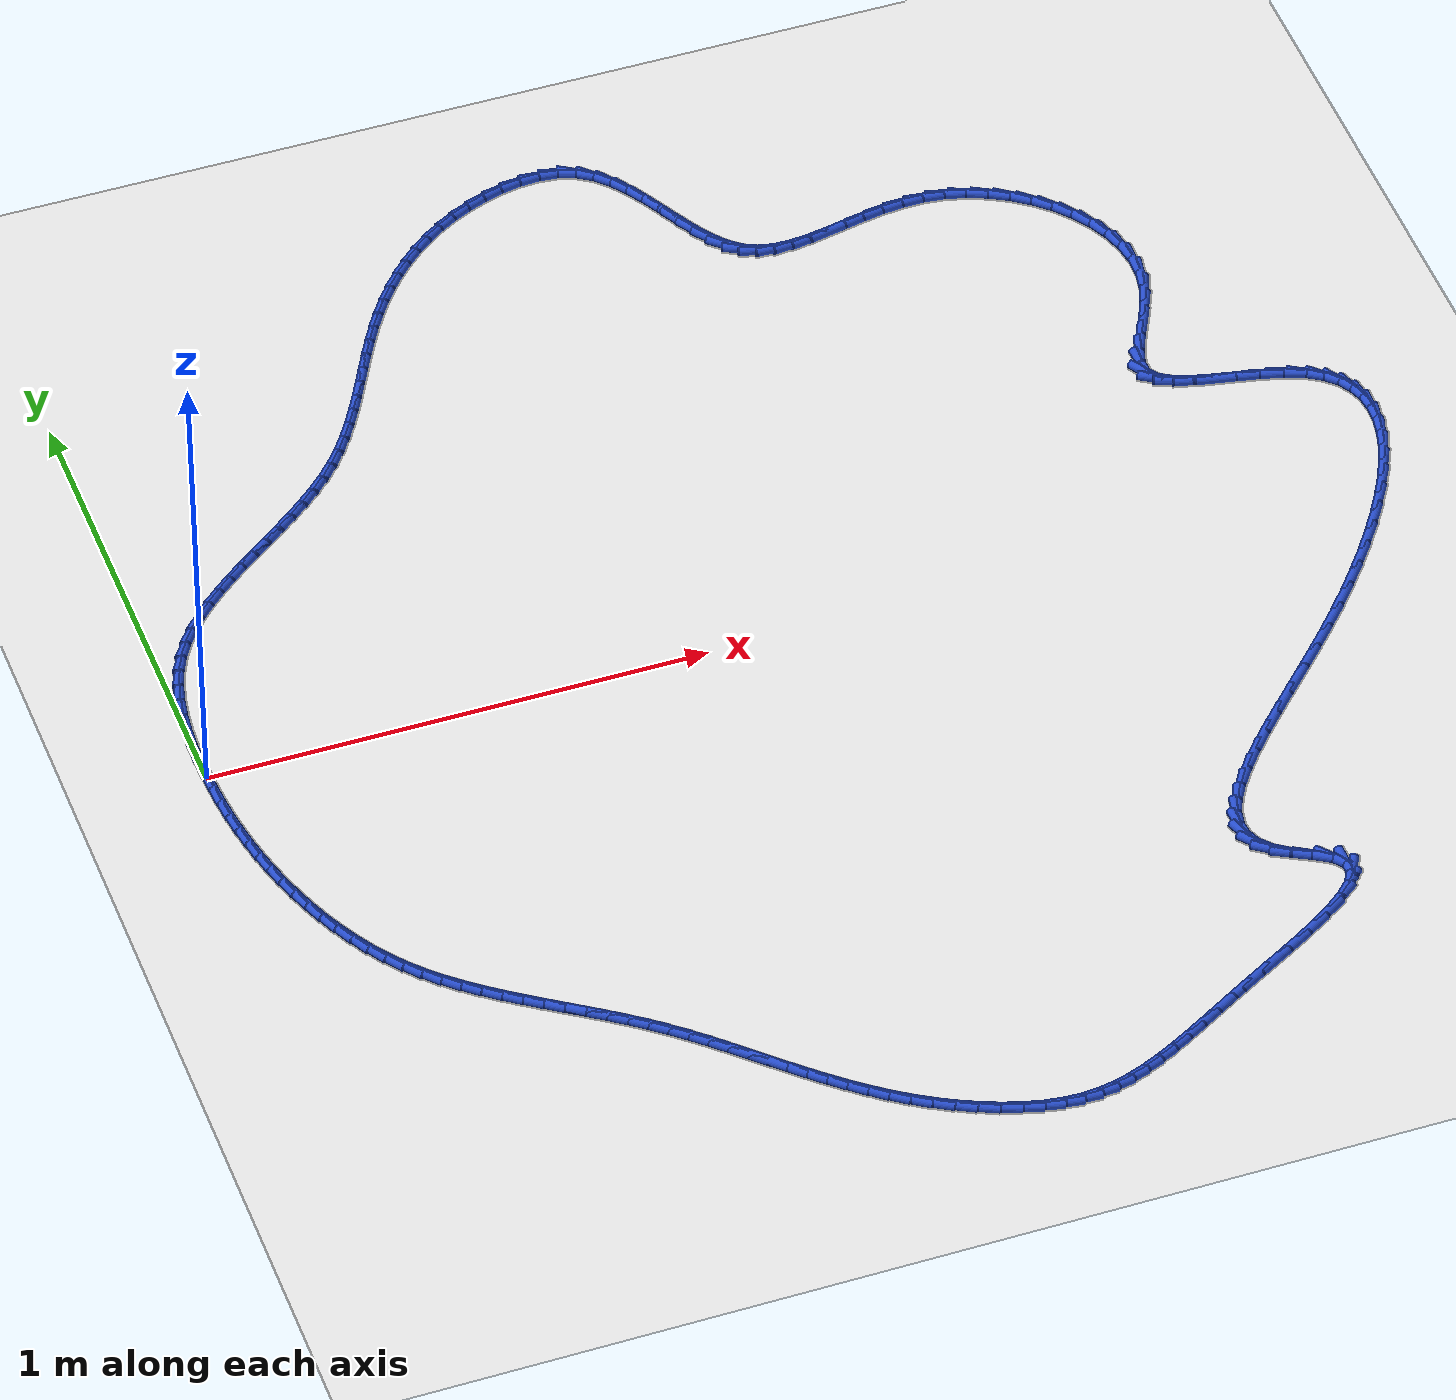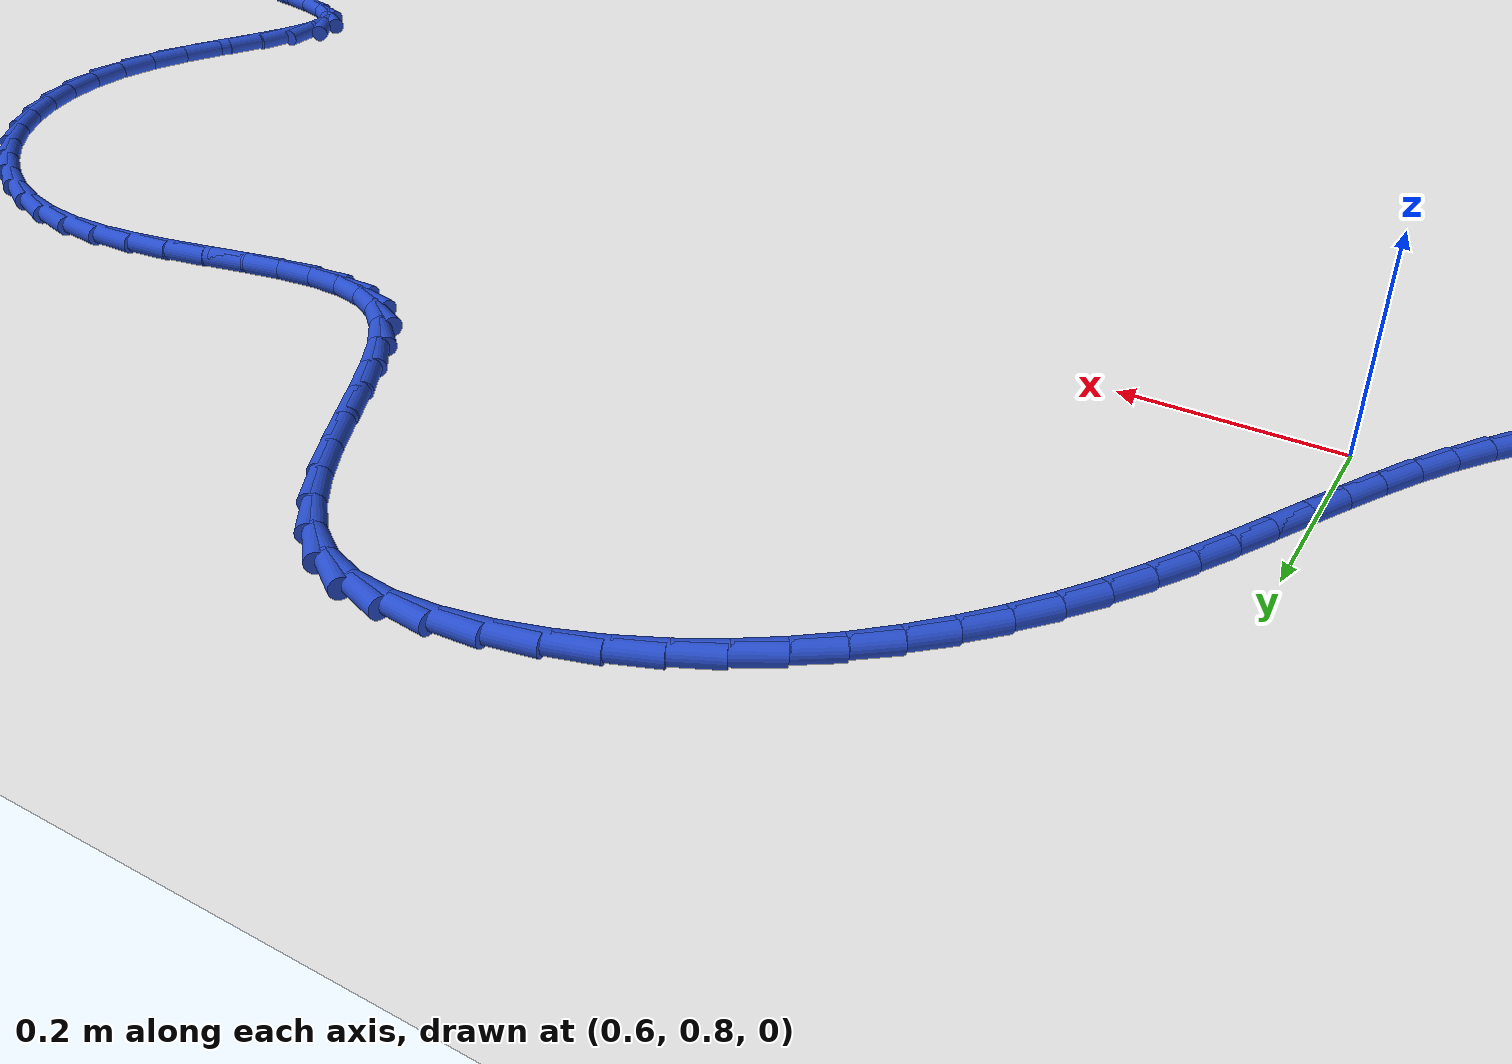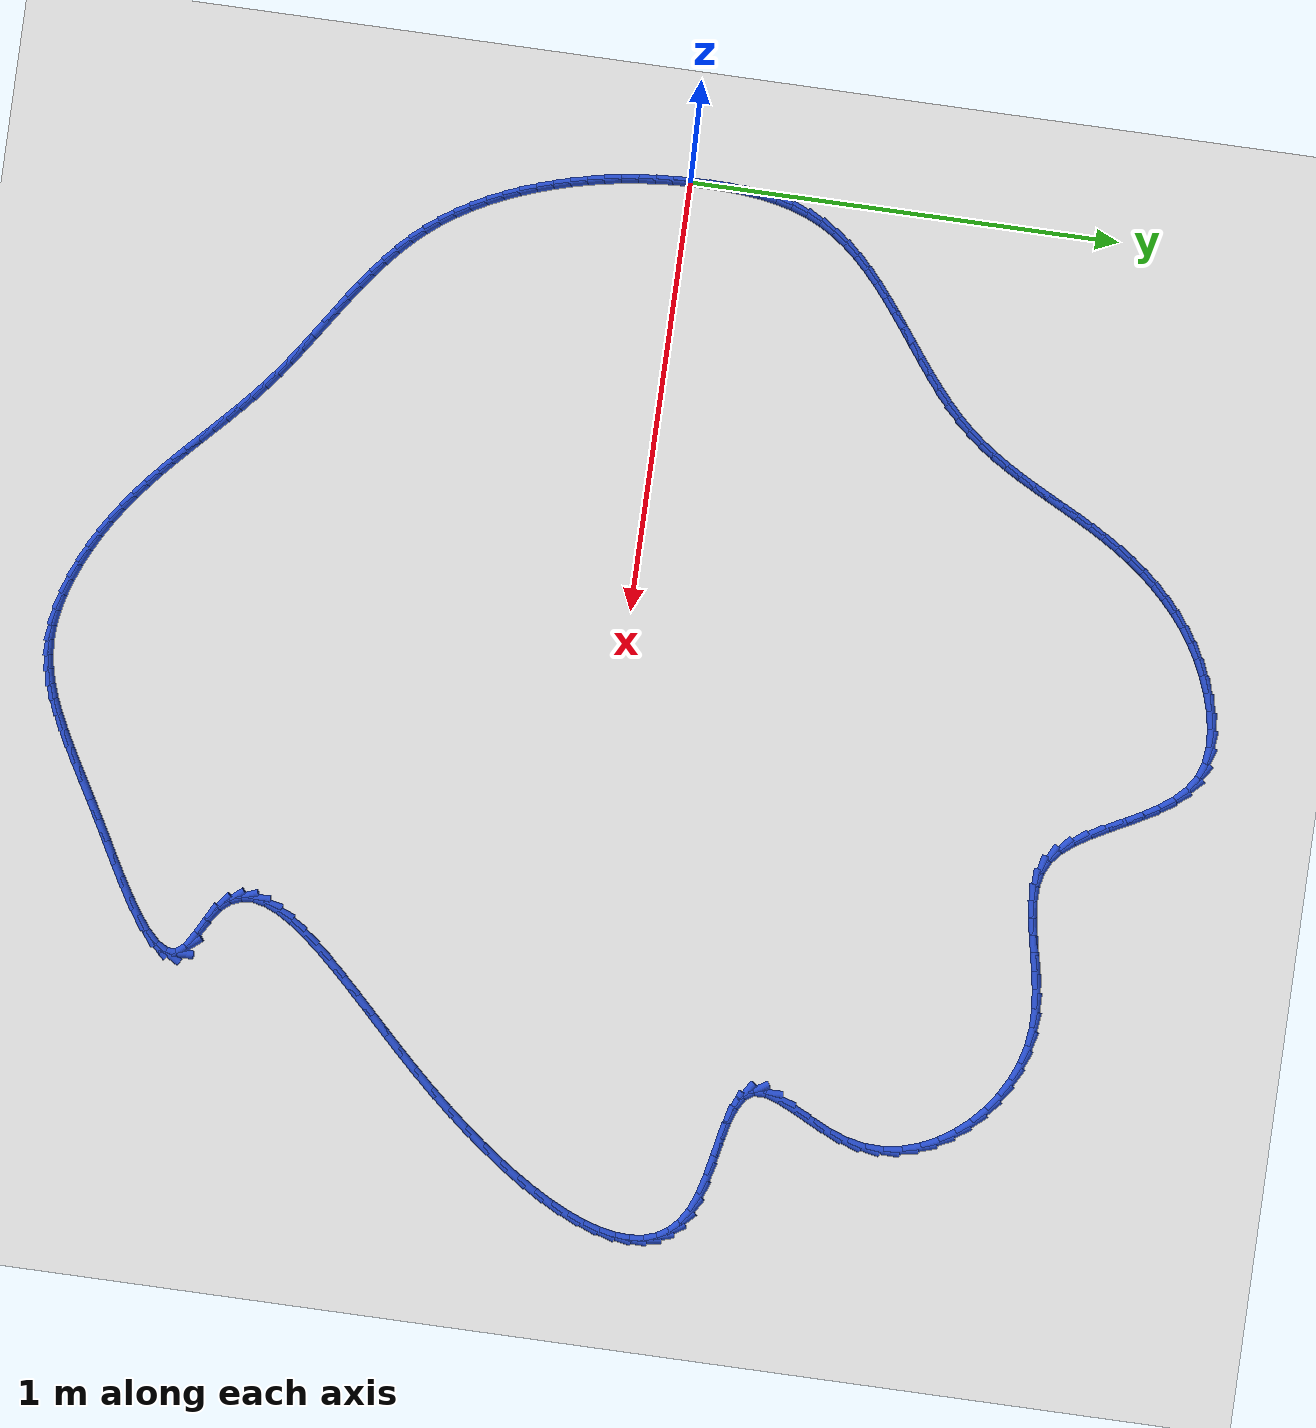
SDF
<sdf version="1.6">
 <world name="default">
  <light name="sun" type="directional">
   <pose>0 0 10 0 -0 0</pose>
   <diffuse>0.8 0.8 0.8 1</diffuse>
   <specular>0.2 0.2 0.2 1</specular>
   <attenuation>
    <range>1000</range>
    <constant>0.9</constant>
    <linear>0.01</linear>
    <quadratic>0.001</quadratic>
   </attenuation>
   <direction>-0.5 0.1 -0.9</direction>
  </light>
  <model name="ground_plane">
   <static>1</static>
   <link name="link">
    <collision name="collision">
     <geometry><plane><normal>0 0 1</normal><size>100 100</size></plane></geometry>
     <surface><friction><ode><mu>100</mu><mu2>50</mu2></ode></friction></surface>
    </collision>
    <visual name="visual">
     <cast_shadows>0</cast_shadows>
     <geometry><plane><normal>0 0 1</normal><size>100 100</size></plane></geometry>
     <material>
      <script><uri>file://media/materials/scripts/gazebo.material</uri><name>Gazebo/WhiteGlow</name></script>
     </material>
    </visual>
   </link>
  </model>
  <gravity>0 0 -9.8</gravity>
  <magnetic_field>6e-06 2.3e-05 -4.2e-05</magnetic_field>
  <atmosphere type="adiabatic"/>
  <physics name="default_physics" default="0" type="ode">
   <max_step_size>0.001</max_step_size>
   <real_time_factor>1</real_time_factor>
   <real_time_update_rate>1000</real_time_update_rate>
  </physics>
  <scene><ambient>0.4 0.4 0.4 1</ambient><background>0.7 0.7 0.7 1</background><shadows>1</shadows></scene>
  <spherical_coordinates>
   <surface_model>EARTH_WGS84</surface_model>
   <latitude_deg>0</latitude_deg>
   <longitude_deg>0</longitude_deg>
   <elevation>0</elevation>
   <heading_deg>0</heading_deg>
  </spherical_coordinates>
  <model name="line">
   <link name="link_0">
    <pose>-1.1275702593849246e-17 -2.7755575615628914e-17 0.01 0 1.57 -1.5521794826872468</pose>
    <collision name="collision">
     <geometry><cylinder><radius>0.01</radius><length>0.08</length></cylinder></geometry>
    </collision>
    <visual name="visual">
     <material>
      <script><name>Gazebo/Blue</name><uri>file://media/materials/scripts/gazebo.material</uri></script>
     </material>
     <geometry><cylinder><radius>0.01</radius><length>0.08</length></cylinder></geometry>
    </visual>
   </link>
   <link name="link_1">
    <pose>-0.0007580148216579398 0.04071190812936072 0.01 0 1.57 1.555061172492371</pose>
    <collision name="collision">
     <geometry><cylinder><radius>0.01</radius><length>0.08</length></cylinder></geometry>
    </collision>
    <visual name="visual">
     <material>
      <script><name>Gazebo/Blue</name><uri>file://media/materials/scripts/gazebo.material</uri></script>
     </material>
     <geometry><cylinder><radius>0.01</radius><length>0.08</length></cylinder></geometry>
    </visual>
   </link>
   <link name="link_2">
    <pose>-0.00011463356133103357 0.08159667784541513 0.01 0 1.57 1.5131589727793138</pose>
    <collision name="collision">
     <geometry><cylinder><radius>0.01</radius><length>0.08</length></cylinder></geometry>
    </collision>
    <visual name="visual">
     <material>
      <script><name>Gazebo/Blue</name><uri>file://media/materials/scripts/gazebo.material</uri></script>
     </material>
     <geometry><cylinder><radius>0.01</radius><length>0.08</length></cylinder></geometry>
    </visual>
   </link>
   <link name="link_3">
    <pose>0.0022349338899343447 0.122316192299354 0.01 0 1.57 1.4627905685262999</pose>
    <collision name="collision">
     <geometry><cylinder><radius>0.01</radius><length>0.08</length></cylinder></geometry>
    </collision>
    <visual name="visual">
     <material>
      <script><name>Gazebo/Blue</name><uri>file://media/materials/scripts/gazebo.material</uri></script>
     </material>
     <geometry><cylinder><radius>0.01</radius><length>0.08</length></cylinder></geometry>
    </visual>
   </link>
   <link name="link_4">
    <pose>0.006595477641091835 0.16253233464236805 0.01 0 1.57 1.4028352260410355</pose>
    <collision name="collision">
     <geometry><cylinder><radius>0.01</radius><length>0.08</length></cylinder></geometry>
    </collision>
    <visual name="visual">
     <material>
      <script><name>Gazebo/Blue</name><uri>file://media/materials/scripts/gazebo.material</uri></script>
     </material>
     <geometry><cylinder><radius>0.01</radius><length>0.08</length></cylinder></geometry>
    </visual>
   </link>
   <link name="link_5">
    <pose>0.013271787801095069 0.20190698802564813 0.01 0 1.57 1.3320342615172331</pose>
    <collision name="collision">
     <geometry><cylinder><radius>0.01</radius><length>0.08</length></cylinder></geometry>
    </collision>
    <visual name="visual">
     <material>
      <script><name>Gazebo/Blue</name><uri>file://media/materials/scripts/gazebo.material</uri></script>
     </material>
     <geometry><cylinder><radius>0.01</radius><length>0.08</length></cylinder></geometry>
    </visual>
   </link>
   <link name="link_6">
    <pose>0.02256865447889768 0.24010203560038498 0.01 0 1.57 1.2491331722972696</pose>
    <collision name="collision">
     <geometry><cylinder><radius>0.01</radius><length>0.08</length></cylinder></geometry>
    </collision>
    <visual name="visual">
     <material>
      <script><name>Gazebo/Blue</name><uri>file://media/materials/scripts/gazebo.material</uri></script>
     </material>
     <geometry><cylinder><radius>0.01</radius><length>0.08</length></cylinder></geometry>
    </visual>
   </link>
   <link name="link_7">
    <pose>0.034790867783453326 0.27677936051776947 0.01 0 1.57 1.1531461597347854</pose>
    <collision name="collision">
     <geometry><cylinder><radius>0.01</radius><length>0.08</length></cylinder></geometry>
    </collision>
    <visual name="visual">
     <material>
      <script><name>Gazebo/Blue</name><uri>file://media/materials/scripts/gazebo.material</uri></script>
     </material>
     <geometry><cylinder><radius>0.01</radius><length>0.08</length></cylinder></geometry>
    </visual>
   </link>
   <link name="link_8">
    <pose>0.05024316654291145 0.311600889601181 0.01 0 1.57 1.0486844006696596</pose>
    <collision name="collision">
     <geometry><cylinder><radius>0.01</radius><length>0.08</length></cylinder></geometry>
    </collision>
    <visual name="visual">
     <material>
      <script><name>Gazebo/Blue</name><uri>file://media/materials/scripts/gazebo.material</uri></script>
     </material>
     <geometry><cylinder><radius>0.01</radius><length>0.08</length></cylinder></geometry>
    </visual>
   </link>
   <link name="link_9">
    <pose>0.06908655645326786 0.34435095688989487 0.01 0 1.57 0.9527006799595094</pose>
    <collision name="collision">
     <geometry><cylinder><radius>0.01</radius><length>0.08</length></cylinder></geometry>
    </collision>
    <visual name="visual">
     <material>
      <script><name>Gazebo/Blue</name><uri>file://media/materials/scripts/gazebo.material</uri></script>
     </material>
     <geometry><cylinder><radius>0.01</radius><length>0.08</length></cylinder></geometry>
    </visual>
   </link>
   <link name="link_10">
    <pose>0.09102414116933398 0.3752038588012029 0.01 0 1.57 0.8699408163419274</pose>
    <collision name="collision">
     <geometry><cylinder><radius>0.01</radius><length>0.08</length></cylinder></geometry>
    </collision>
    <visual name="visual">
     <material>
      <script><name>Gazebo/Blue</name><uri>file://media/materials/scripts/gazebo.material</uri></script>
     </material>
     <geometry><cylinder><radius>0.01</radius><length>0.08</length></cylinder></geometry>
    </visual>
   </link>
   <link name="link_11">
    <pose>0.1156680396771172 0.404411376879386 0.01 0 1.57 0.8009435129025211</pose>
    <collision name="collision">
     <geometry><cylinder><radius>0.01</radius><length>0.08</length></cylinder></geometry>
    </collision>
    <visual name="visual">
     <material>
      <script><name>Gazebo/Blue</name><uri>file://media/materials/scripts/gazebo.material</uri></script>
     </material>
     <geometry><cylinder><radius>0.01</radius><length>0.08</length></cylinder></geometry>
    </visual>
   </link>
   <link name="link_12">
    <pose>0.1426303709626249 0.4322252926687254 0.01 0 1.57 0.7454520188675524</pose>
    <collision name="collision">
     <geometry><cylinder><radius>0.01</radius><length>0.08</length></cylinder></geometry>
    </collision>
    <visual name="visual">
     <material>
      <script><name>Gazebo/Blue</name><uri>file://media/materials/scripts/gazebo.material</uri></script>
     </material>
     <geometry><cylinder><radius>0.01</radius><length>0.08</length></cylinder></geometry>
    </visual>
   </link>
   <link name="link_13">
    <pose>0.17152325401186455 0.45889738771350214 0.01 0 1.57 0.7028099325533932</pose>
    <collision name="collision">
     <geometry><cylinder><radius>0.01</radius><length>0.08</length></cylinder></geometry>
    </collision>
    <visual name="visual">
     <material>
      <script><name>Gazebo/Blue</name><uri>file://media/materials/scripts/gazebo.material</uri></script>
     </material>
     <geometry><cylinder><radius>0.01</radius><length>0.08</length></cylinder></geometry>
    </visual>
   </link>
   <link name="link_14">
    <pose>0.20195880781084358 0.48467944355799736 0.01 0 1.57 0.6722561646299304</pose>
    <collision name="collision">
     <geometry><cylinder><radius>0.01</radius><length>0.08</length></cylinder></geometry>
    </collision>
    <visual name="visual">
     <material>
      <script><name>Gazebo/Blue</name><uri>file://media/materials/scripts/gazebo.material</uri></script>
     </material>
     <geometry><cylinder><radius>0.01</radius><length>0.08</length></cylinder></geometry>
    </visual>
   </link>
   <link name="link_15">
    <pose>0.23354915134556925 0.509823241746492 0.01 0 1.57 0.6531106419826347</pose>
    <collision name="collision">
     <geometry><cylinder><radius>0.01</radius><length>0.08</length></cylinder></geometry>
    </collision>
    <visual name="visual">
     <material>
      <script><name>Gazebo/Blue</name><uri>file://media/materials/scripts/gazebo.material</uri></script>
     </material>
     <geometry><cylinder><radius>0.01</radius><length>0.08</length></cylinder></geometry>
    </visual>
   </link>
   <link name="link_16">
    <pose>0.2659064036020491 0.534580563823267 0.01 0 1.57 0.6448763631168236</pose>
    <collision name="collision">
     <geometry><cylinder><radius>0.01</radius><length>0.08</length></cylinder></geometry>
    </collision>
    <visual name="visual">
     <material>
      <script><name>Gazebo/Blue</name><uri>file://media/materials/scripts/gazebo.material</uri></script>
     </material>
     <geometry><cylinder><radius>0.01</radius><length>0.08</length></cylinder></geometry>
    </visual>
   </link>
   <link name="link_17">
    <pose>0.29864268356629053 0.559203191332604 0.01 0 1.57 0.6472868964107775</pose>
    <collision name="collision">
     <geometry><cylinder><radius>0.01</radius><length>0.08</length></cylinder></geometry>
    </collision>
    <visual name="visual">
     <material>
      <script><name>Gazebo/Blue</name><uri>file://media/materials/scripts/gazebo.material</uri></script>
     </material>
     <geometry><cylinder><radius>0.01</radius><length>0.08</length></cylinder></geometry>
    </visual>
   </link>
   <link name="link_18">
    <pose>0.33137011022430085 0.5839429058187836 0.01 0 1.57 0.6603198498563069</pose>
    <collision name="collision">
     <geometry><cylinder><radius>0.01</radius><length>0.08</length></cylinder></geometry>
    </collision>
    <visual name="visual">
     <material>
      <script><name>Gazebo/Blue</name><uri>file://media/materials/scripts/gazebo.material</uri></script>
     </material>
     <geometry><cylinder><radius>0.01</radius><length>0.08</length></cylinder></geometry>
    </visual>
   </link>
   <link name="link_19">
    <pose>0.36370080256208753 0.6090514888260867 0.01 0 1.57 0.6841858280186689</pose>
    <collision name="collision">
     <geometry><cylinder><radius>0.01</radius><length>0.08</length></cylinder></geometry>
    </collision>
    <visual name="visual">
     <material>
      <script><name>Gazebo/Blue</name><uri>file://media/materials/scripts/gazebo.material</uri></script>
     </material>
     <geometry><cylinder><radius>0.01</radius><length>0.08</length></cylinder></geometry>
    </visual>
   </link>
   <link name="link_20">
    <pose>0.39524687956565807 0.6347807218987951 0.01 0 1.57 0.7192919118300661</pose>
    <collision name="collision">
     <geometry><cylinder><radius>0.01</radius><length>0.08</length></cylinder></geometry>
    </collision>
    <visual name="visual">
     <material>
      <script><name>Gazebo/Blue</name><uri>file://media/materials/scripts/gazebo.material</uri></script>
     </material>
     <geometry><cylinder><radius>0.01</radius><length>0.08</length></cylinder></geometry>
    </visual>
   </link>
   <link name="link_21">
    <pose>0.4256204602210196 0.6613823865811892 0.01 0 1.57 0.7661691377934439</pose>
    <collision name="collision">
     <geometry><cylinder><radius>0.01</radius><length>0.08</length></cylinder></geometry>
    </collision>
    <visual name="visual">
     <material>
      <script><name>Gazebo/Blue</name><uri>file://media/materials/scripts/gazebo.material</uri></script>
     </material>
     <geometry><cylinder><radius>0.01</radius><length>0.08</length></cylinder></geometry>
    </visual>
   </link>
   <link name="link_22">
    <pose>0.4544336635141799 0.6891082644175504 0.01 0 1.57 0.8253457193741824</pose>
    <collision name="collision">
     <geometry><cylinder><radius>0.01</radius><length>0.08</length></cylinder></geometry>
    </collision>
    <visual name="visual">
     <material>
      <script><name>Gazebo/Blue</name><uri>file://media/materials/scripts/gazebo.material</uri></script>
     </material>
     <geometry><cylinder><radius>0.01</radius><length>0.08</length></cylinder></geometry>
    </visual>
   </link>
   <link name="link_23">
    <pose>0.4812986084408836 0.7182101369457274 0.01 0 1.57 0.8933440506550244</pose>
    <collision name="collision">
     <geometry><cylinder><radius>0.01</radius><length>0.08</length></cylinder></geometry>
    </collision>
    <visual name="visual">
     <material>
      <script><name>Gazebo/Blue</name><uri>file://media/materials/scripts/gazebo.material</uri></script>
     </material>
     <geometry><cylinder><radius>0.01</radius><length>0.08</length></cylinder></geometry>
    </visual>
   </link>
   <link name="link_24">
    <pose>0.5059526958101064 0.7488570328154204 0.01 0 1.57 0.9548218915692187</pose>
    <collision name="collision">
     <geometry><cylinder><radius>0.01</radius><length>0.08</length></cylinder></geometry>
    </collision>
    <visual name="visual">
     <material>
      <script><name>Gazebo/Blue</name><uri>file://media/materials/scripts/gazebo.material</uri></script>
     </material>
     <geometry><cylinder><radius>0.01</radius><length>0.08</length></cylinder></geometry>
    </visual>
   </link>
   <link name="link_25">
    <pose>0.5286280516902501 0.7808911978576369 0.01 0 1.57 1.0054759125805273</pose>
    <collision name="collision">
     <geometry><cylinder><radius>0.01</radius><length>0.08</length></cylinder></geometry>
    </collision>
    <visual name="visual">
     <material>
      <script><name>Gazebo/Blue</name><uri>file://media/materials/scripts/gazebo.material</uri></script>
     </material>
     <geometry><cylinder><radius>0.01</radius><length>0.08</length></cylinder></geometry>
    </visual>
   </link>
   <link name="link_26">
    <pose>0.5496789033605138 0.8140742259110534 0.01 0 1.57 1.0450730989019015</pose>
    <collision name="collision">
     <geometry><cylinder><radius>0.01</radius><length>0.08</length></cylinder></geometry>
    </collision>
    <visual name="visual">
     <material>
      <script><name>Gazebo/Blue</name><uri>file://media/materials/scripts/gazebo.material</uri></script>
     </material>
     <geometry><cylinder><radius>0.01</radius><length>0.08</length></cylinder></geometry>
    </visual>
   </link>
   <link name="link_27">
    <pose>0.5694594781000962 0.8481677108143462 0.01 0 1.57 1.0736356791171813</pose>
    <collision name="collision">
     <geometry><cylinder><radius>0.01</radius><length>0.08</length></cylinder></geometry>
    </collision>
    <visual name="visual">
     <material>
      <script><name>Gazebo/Blue</name><uri>file://media/materials/scripts/gazebo.material</uri></script>
     </material>
     <geometry><cylinder><radius>0.01</radius><length>0.08</length></cylinder></geometry>
    </visual>
   </link>
   <link name="link_28">
    <pose>0.5883240031881958 0.8829332464061914 0.01 0 1.57 1.0912965118283868</pose>
    <collision name="collision">
     <geometry><cylinder><radius>0.01</radius><length>0.08</length></cylinder></geometry>
    </collision>
    <visual name="visual">
     <material>
      <script><name>Gazebo/Blue</name><uri>file://media/materials/scripts/gazebo.material</uri></script>
     </material>
     <geometry><cylinder><radius>0.01</radius><length>0.08</length></cylinder></geometry>
    </visual>
   </link>
   <link name="link_29">
    <pose>0.6066267059040114 0.9181324265252656 0.01 0 1.57 1.0981957454495095</pose>
    <collision name="collision">
     <geometry><cylinder><radius>0.01</radius><length>0.08</length></cylinder></geometry>
    </collision>
    <visual name="visual">
     <material>
      <script><name>Gazebo/Blue</name><uri>file://media/materials/scripts/gazebo.material</uri></script>
     </material>
     <geometry><cylinder><radius>0.01</radius><length>0.08</length></cylinder></geometry>
    </visual>
   </link>
   <link name="link_30">
    <pose>0.6247218135267418 0.9535268450102449 0.01 0 1.57 1.0944197567955964</pose>
    <collision name="collision">
     <geometry><cylinder><radius>0.01</radius><length>0.08</length></cylinder></geometry>
    </collision>
    <visual name="visual">
     <material>
      <script><name>Gazebo/Blue</name><uri>file://media/materials/scripts/gazebo.material</uri></script>
     </material>
     <geometry><cylinder><radius>0.01</radius><length>0.08</length></cylinder></geometry>
    </visual>
   </link>
   <link name="link_31">
    <pose>0.6429635533355856 0.9888780956998058 0.01 0 1.57 1.079978664449211</pose>
    <collision name="collision">
     <geometry><cylinder><radius>0.01</radius><length>0.08</length></cylinder></geometry>
    </collision>
    <visual name="visual">
     <material>
      <script><name>Gazebo/Blue</name><uri>file://media/materials/scripts/gazebo.material</uri></script>
     </material>
     <geometry><cylinder><radius>0.01</radius><length>0.08</length></cylinder></geometry>
    </visual>
   </link>
   <link name="link_32">
    <pose>0.6617061526097416 1.0239477724326247 0.01 0 1.57 1.0548196645291898</pose>
    <collision name="collision">
     <geometry><cylinder><radius>0.01</radius><length>0.08</length></cylinder></geometry>
    </collision>
    <visual name="visual">
     <material>
      <script><name>Gazebo/Blue</name><uri>file://media/materials/scripts/gazebo.material</uri></script>
     </material>
     <geometry><cylinder><radius>0.01</radius><length>0.08</length></cylinder></geometry>
    </visual>
   </link>
   <link name="link_33">
    <pose>0.6813038386284085 1.0584974690473774 0.01 0 1.57 1.0188998135889233</pose>
    <collision name="collision">
     <geometry><cylinder><radius>0.01</radius><length>0.08</length></cylinder></geometry>
    </collision>
    <visual name="visual">
     <material>
      <script><name>Gazebo/Blue</name><uri>file://media/materials/scripts/gazebo.material</uri></script>
     </material>
     <geometry><cylinder><radius>0.01</radius><length>0.08</length></cylinder></geometry>
    </visual>
   </link>
   <link name="link_34">
    <pose>0.7021098673235646 1.0922889776427565 0.01 0 1.57 0.9743697836934179</pose>
    <collision name="collision">
     <geometry><cylinder><radius>0.01</radius><length>0.08</length></cylinder></geometry>
    </collision>
    <visual name="visual">
     <material>
      <script><name>Gazebo/Blue</name><uri>file://media/materials/scripts/gazebo.material</uri></script>
     </material>
     <geometry><cylinder><radius>0.01</radius><length>0.08</length></cylinder></geometry>
    </visual>
   </link>
   <link name="link_35">
    <pose>0.7243871114631888 1.1251025382700675 0.01 0 1.57 0.925034121604187</pose>
    <collision name="collision">
     <geometry><cylinder><radius>0.01</radius><length>0.08</length></cylinder></geometry>
    </collision>
    <visual name="visual">
     <material>
      <script><name>Gazebo/Blue</name><uri>file://media/materials/scripts/gazebo.material</uri></script>
     </material>
     <geometry><cylinder><radius>0.01</radius><length>0.08</length></cylinder></geometry>
    </visual>
   </link>
   <link name="link_36">
    <pose>0.7482358899334995 1.1567515695746766 0.01 0 1.57 0.8711605030415978</pose>
    <collision name="collision">
     <geometry><cylinder><radius>0.01</radius><length>0.08</length></cylinder></geometry>
    </collision>
    <visual name="visual">
     <material>
      <script><name>Gazebo/Blue</name><uri>file://media/materials/scripts/gazebo.material</uri></script>
     </material>
     <geometry><cylinder><radius>0.01</radius><length>0.08</length></cylinder></geometry>
    </visual>
   </link>
   <link name="link_37">
    <pose>0.7737395381273396 1.187052956673658 0.01 0 1.57 0.8126848541861744</pose>
    <collision name="collision">
     <geometry><cylinder><radius>0.01</radius><length>0.08</length></cylinder></geometry>
    </collision>
    <visual name="visual">
     <material>
      <script><name>Gazebo/Blue</name><uri>file://media/materials/scripts/gazebo.material</uri></script>
     </material>
     <geometry><cylinder><radius>0.01</radius><length>0.08</length></cylinder></geometry>
    </visual>
   </link>
   <link name="link_38">
    <pose>0.8009813914375513 1.215823584684088 0.01 0 1.57 0.7496572512925318</pose>
    <collision name="collision">
     <geometry><cylinder><radius>0.01</radius><length>0.08</length></cylinder></geometry>
    </collision>
    <visual name="visual">
     <material>
      <script><name>Gazebo/Blue</name><uri>file://media/materials/scripts/gazebo.material</uri></script>
     </material>
     <geometry><cylinder><radius>0.01</radius><length>0.08</length></cylinder></geometry>
    </visual>
   </link>
   <link name="link_39">
    <pose>0.8300447852569769 1.24288033872304 0.01 0 1.57 0.6822785478303901</pose>
    <collision name="collision">
     <geometry><cylinder><radius>0.01</radius><length>0.08</length></cylinder></geometry>
    </collision>
    <visual name="visual">
     <material>
      <script><name>Gazebo/Blue</name><uri>file://media/materials/scripts/gazebo.material</uri></script>
     </material>
     <geometry><cylinder><radius>0.01</radius><length>0.08</length></cylinder></geometry>
    </visual>
   </link>
   <link name="link_40">
    <pose>0.8610130549784595 1.2680401039075897 0.01 0 1.57 0.6109321194084202</pose>
    <collision name="collision">
     <geometry><cylinder><radius>0.01</radius><length>0.08</length></cylinder></geometry>
    </collision>
    <visual name="visual">
     <material>
      <script><name>Gazebo/Blue</name><uri>file://media/materials/scripts/gazebo.material</uri></script>
     </material>
     <geometry><cylinder><radius>0.01</radius><length>0.08</length></cylinder></geometry>
    </visual>
   </link>
   <link name="link_41">
    <pose>0.8939695359948407 1.2911197653548114 0.01 0 1.57 0.5362027180537691</pose>
    <collision name="collision">
     <geometry><cylinder><radius>0.01</radius><length>0.08</length></cylinder></geometry>
    </collision>
    <visual name="visual">
     <material>
      <script><name>Gazebo/Blue</name><uri>file://media/materials/scripts/gazebo.material</uri></script>
     </material>
     <geometry><cylinder><radius>0.01</radius><length>0.08</length></cylinder></geometry>
    </visual>
   </link>
   <link name="link_42">
    <pose>0.9289975636989636 1.3119362081817805 0.01 0 1.57 0.4588739707812287</pose>
    <collision name="collision">
     <geometry><cylinder><radius>0.01</radius><length>0.08</length></cylinder></geometry>
    </collision>
    <visual name="visual">
     <material>
      <script><name>Gazebo/Blue</name><uri>file://media/materials/scripts/gazebo.material</uri></script>
     </material>
     <geometry><cylinder><radius>0.01</radius><length>0.08</length></cylinder></geometry>
    </visual>
   </link>
   <link name="link_43">
    <pose>0.966180473483671 1.3303063175055723 0.01 0 1.57 0.3797169198946685</pose>
    <collision name="collision">
     <geometry><cylinder><radius>0.01</radius><length>0.08</length></cylinder></geometry>
    </collision>
    <visual name="visual">
     <material>
      <script><name>Gazebo/Blue</name><uri>file://media/materials/scripts/gazebo.material</uri></script>
     </material>
     <geometry><cylinder><radius>0.01</radius><length>0.08</length></cylinder></geometry>
    </visual>
   </link>
   <link name="link_44">
    <pose>1.0055745547148298 1.3460278854466672 0.01 0 1.57 0.2940314925303402</pose>
    <collision name="collision">
     <geometry><cylinder><radius>0.01</radius><length>0.08</length></cylinder></geometry>
    </collision>
    <visual name="visual">
     <material>
      <script><name>Gazebo/Blue</name><uri>file://media/materials/scripts/gazebo.material</uri></script>
     </material>
     <geometry><cylinder><radius>0.01</radius><length>0.08</length></cylinder></geometry>
    </visual>
   </link>
   <link name="link_45">
    <pose>1.0466026985848493 1.358451560107704 0.01 0 1.57 0.19125689723136152</pose>
    <collision name="collision">
     <geometry><cylinder><radius>0.01</radius><length>0.08</length></cylinder></geometry>
    </collision>
    <visual name="visual">
     <material>
      <script><name>Gazebo/Blue</name><uri>file://media/materials/scripts/gazebo.material</uri></script>
     </material>
     <geometry><cylinder><radius>0.01</radius><length>0.08</length></cylinder></geometry>
    </visual>
   </link>
   <link name="link_46">
    <pose>1.0880480335678888 1.3664763525574763 0.01 0 1.57 0.06159343413394013</pose>
    <collision name="collision">
     <geometry><cylinder><radius>0.01</radius><length>0.08</length></cylinder></geometry>
    </collision>
    <visual name="visual">
     <material>
      <script><name>Gazebo/Blue</name><uri>file://media/materials/scripts/gazebo.material</uri></script>
     </material>
     <geometry><cylinder><radius>0.01</radius><length>0.08</length></cylinder></geometry>
    </visual>
   </link>
   <link name="link_47">
    <pose>1.1286653691622865 1.3689812822368241 0.01 0 1.57 -0.10689428216040722</pose>
    <collision name="collision">
     <geometry><cylinder><radius>0.01</radius><length>0.08</length></cylinder></geometry>
    </collision>
    <visual name="visual">
     <material>
      <script><name>Gazebo/Blue</name><uri>file://media/materials/scripts/gazebo.material</uri></script>
     </material>
     <geometry><cylinder><radius>0.01</radius><length>0.08</length></cylinder></geometry>
    </visual>
   </link>
   <link name="link_48">
    <pose>1.1672095148663804 1.364845368586588 0.01 0 1.57 -0.32572626954739164</pose>
    <collision name="collision">
     <geometry><cylinder><radius>0.01</radius><length>0.08</length></cylinder></geometry>
    </collision>
    <visual name="visual">
     <material>
      <script><name>Gazebo/Blue</name><uri>file://media/materials/scripts/gazebo.material</uri></script>
     </material>
     <geometry><cylinder><radius>0.01</radius><length>0.08</length></cylinder></geometry>
    </visual>
   </link>
   <link name="link_49">
    <pose>1.2024352801785085 1.3529476310476076 0.01 0 1.57 -0.5806431461620517</pose>
    <collision name="collision">
     <geometry><cylinder><radius>0.01</radius><length>0.08</length></cylinder></geometry>
    </collision>
    <visual name="visual">
     <material>
      <script><name>Gazebo/Blue</name><uri>file://media/materials/scripts/gazebo.material</uri></script>
     </material>
     <geometry><cylinder><radius>0.01</radius><length>0.08</length></cylinder></geometry>
    </visual>
   </link>
   <link name="link_50">
    <pose>1.2334210359245696 1.3326182469742145 0.01 0 1.57 -0.7914961781277791</pose>
    <collision name="collision">
     <geometry><cylinder><radius>0.01</radius><length>0.08</length></cylinder></geometry>
    </collision>
    <visual name="visual">
     <material>
      <script><name>Gazebo/Blue</name><uri>file://media/materials/scripts/gazebo.material</uri></script>
     </material>
     <geometry><cylinder><radius>0.01</radius><length>0.08</length></cylinder></geometry>
    </visual>
   </link>
   <link name="link_51">
    <pose>1.2606121515067468 1.3050934689308822 0.01 0 1.57 -0.9377124161625547</pose>
    <collision name="collision">
     <geometry><cylinder><radius>0.01</radius><length>0.08</length></cylinder></geometry>
    </collision>
    <visual name="visual">
     <material>
      <script><name>Gazebo/Blue</name><uri>file://media/materials/scripts/gazebo.material</uri></script>
     </material>
     <geometry><cylinder><radius>0.01</radius><length>0.08</length></cylinder></geometry>
    </visual>
   </link>
   <link name="link_52">
    <pose>1.2848149451744901 1.2721128387040617 0.01 0 1.57 -1.0303241424602596</pose>
    <collision name="collision">
     <geometry><cylinder><radius>0.01</radius><length>0.08</length></cylinder></geometry>
    </collision>
    <visual name="visual">
     <material>
      <script><name>Gazebo/Blue</name><uri>file://media/materials/scripts/gazebo.material</uri></script>
     </material>
     <geometry><cylinder><radius>0.01</radius><length>0.08</length></cylinder></geometry>
    </visual>
   </link>
   <link name="link_53">
    <pose>1.3068357372475137 1.235415900966877 0.01 0 1.57 -1.0804538263771792</pose>
    <collision name="collision">
     <geometry><cylinder><radius>0.01</radius><length>0.08</length></cylinder></geometry>
    </collision>
    <visual name="visual">
     <material>
      <script><name>Gazebo/Blue</name><uri>file://media/materials/scripts/gazebo.material</uri></script>
     </material>
     <geometry><cylinder><radius>0.01</radius><length>0.08</length></cylinder></geometry>
    </visual>
   </link>
   <link name="link_54">
    <pose>1.3274808480455298 1.1967422003924517 0.01 0 1.57 -1.0944771639709912</pose>
    <collision name="collision">
     <geometry><cylinder><radius>0.01</radius><length>0.08</length></cylinder></geometry>
    </collision>
    <visual name="visual">
     <material>
      <script><name>Gazebo/Blue</name><uri>file://media/materials/scripts/gazebo.material</uri></script>
     </material>
     <geometry><cylinder><radius>0.01</radius><length>0.08</length></cylinder></geometry>
    </visual>
   </link>
   <link name="link_55">
    <pose>1.3475565978882513 1.1578312816539087 0.01 0 1.57 -1.0733465048747826</pose>
    <collision name="collision">
     <geometry><cylinder><radius>0.01</radius><length>0.08</length></cylinder></geometry>
    </collision>
    <visual name="visual">
     <material>
      <script><name>Gazebo/Blue</name><uri>file://media/materials/scripts/gazebo.material</uri></script>
     </material>
     <geometry><cylinder><radius>0.01</radius><length>0.08</length></cylinder></geometry>
    </visual>
   </link>
   <link name="link_56">
    <pose>1.3678693070953918 1.1204226894243716 0.01 0 1.57 -1.0121593756264433</pose>
    <collision name="collision">
     <geometry><cylinder><radius>0.01</radius><length>0.08</length></cylinder></geometry>
    </collision>
    <visual name="visual">
     <material>
      <script><name>Gazebo/Blue</name><uri>file://media/materials/scripts/gazebo.material</uri></script>
     </material>
     <geometry><cylinder><radius>0.01</radius><length>0.08</length></cylinder></geometry>
    </visual>
   </link>
   <link name="link_57">
    <pose>1.3892252959866644 1.0862559683769637 0.01 0 1.57 -0.8990429343614283</pose>
    <collision name="collision">
     <geometry><cylinder><radius>0.01</radius><length>0.08</length></cylinder></geometry>
    </collision>
    <visual name="visual">
     <material>
      <script><name>Gazebo/Blue</name><uri>file://media/materials/scripts/gazebo.material</uri></script>
     </material>
     <geometry><cylinder><radius>0.01</radius><length>0.08</length></cylinder></geometry>
    </visual>
   </link>
   <link name="link_58">
    <pose>1.412430884881781 1.0570706631848086 0.01 0 1.57 -0.7152165748143586</pose>
    <collision name="collision">
     <geometry><cylinder><radius>0.01</radius><length>0.08</length></cylinder></geometry>
    </collision>
    <visual name="visual">
     <material>
      <script><name>Gazebo/Blue</name><uri>file://media/materials/scripts/gazebo.material</uri></script>
     </material>
     <geometry><cylinder><radius>0.01</radius><length>0.08</length></cylinder></geometry>
    </visual>
   </link>
   <link name="link_59">
    <pose>1.4382923941004557 1.0346063185210292 0.01 0 1.57 -0.45557709242875116</pose>
    <collision name="collision">
     <geometry><cylinder><radius>0.01</radius><length>0.08</length></cylinder></geometry>
    </collision>
    <visual name="visual">
     <material>
      <script><name>Gazebo/Blue</name><uri>file://media/materials/scripts/gazebo.material</uri></script>
     </material>
     <geometry><cylinder><radius>0.01</radius><length>0.08</length></cylinder></geometry>
    </visual>
   </link>
   <link name="link_60">
    <pose>1.467500588903379 1.0202956997544859 0.01 0 1.57 -0.20590621221302952</pose>
    <collision name="collision">
     <geometry><cylinder><radius>0.01</radius><length>0.08</length></cylinder></geometry>
    </collision>
    <visual name="visual">
     <material>
      <script><name>Gazebo/Blue</name><uri>file://media/materials/scripts/gazebo.material</uri></script>
     </material>
     <geometry><cylinder><radius>0.01</radius><length>0.08</length></cylinder></geometry>
    </visual>
   </link>
   <link name="link_61">
    <pose>1.499971093541033 1.0135137028554233 0.01 0 1.57 -0.020512684227536018</pose>
    <collision name="collision">
     <geometry><cylinder><radius>0.01</radius><length>0.08</length></cylinder></geometry>
    </collision>
    <visual name="visual">
     <material>
      <script><name>Gazebo/Blue</name><uri>file://media/materials/scripts/gazebo.material</uri></script>
     </material>
     <geometry><cylinder><radius>0.01</radius><length>0.08</length></cylinder></geometry>
    </visual>
   </link>
   <link name="link_62">
    <pose>1.5353007443059836 1.0127888952234068 0.01 0 1.57 0.10176123029134934</pose>
    <collision name="collision">
     <geometry><cylinder><radius>0.01</radius><length>0.08</length></cylinder></geometry>
    </collision>
    <visual name="visual">
     <material>
      <script><name>Gazebo/Blue</name><uri>file://media/materials/scripts/gazebo.material</uri></script>
     </material>
     <geometry><cylinder><radius>0.01</radius><length>0.08</length></cylinder></geometry>
    </visual>
   </link>
   <link name="link_63">
    <pose>1.5730853946899688 1.0166472350866085 0.01 0 1.57 0.17315389826971428</pose>
    <collision name="collision">
     <geometry><cylinder><radius>0.01</radius><length>0.08</length></cylinder></geometry>
    </collision>
    <visual name="visual">
     <material>
      <script><name>Gazebo/Blue</name><uri>file://media/materials/scripts/gazebo.material</uri></script>
     </material>
     <geometry><cylinder><radius>0.01</radius><length>0.08</length></cylinder></geometry>
    </visual>
   </link>
   <link name="link_64">
    <pose>1.612920898184726 1.0236146806732014 0.01 0 1.57 0.20447989285121526</pose>
    <collision name="collision">
     <geometry><cylinder><radius>0.01</radius><length>0.08</length></cylinder></geometry>
    </collision>
    <visual name="visual">
     <material>
      <script><name>Gazebo/Blue</name><uri>file://media/materials/scripts/gazebo.material</uri></script>
     </material>
     <geometry><cylinder><radius>0.01</radius><length>0.08</length></cylinder></geometry>
    </visual>
   </link>
   <link name="link_65">
    <pose>1.6544031082819934 1.032217190211358 0.01 0 1.57 0.2023098656296809</pose>
    <collision name="collision">
     <geometry><cylinder><radius>0.01</radius><length>0.08</length></cylinder></geometry>
    </collision>
    <visual name="visual">
     <material>
      <script><name>Gazebo/Blue</name><uri>file://media/materials/scripts/gazebo.material</uri></script>
     </material>
     <geometry><cylinder><radius>0.01</radius><length>0.08</length></cylinder></geometry>
    </visual>
   </link>
   <link name="link_66">
    <pose>1.6971278784735082 1.0409807219292506 0.01 0 1.57 0.1693888432417191</pose>
    <collision name="collision">
     <geometry><cylinder><radius>0.01</radius><length>0.08</length></cylinder></geometry>
    </collision>
    <visual name="visual">
     <material>
      <script><name>Gazebo/Blue</name><uri>file://media/materials/scripts/gazebo.material</uri></script>
     </material>
     <geometry><cylinder><radius>0.01</radius><length>0.08</length></cylinder></geometry>
    </visual>
   </link>
   <link name="link_67">
    <pose>1.7406910622510083 1.0484312340550526 0.01 0 1.57 0.10559937835502822</pose>
    <collision name="collision">
     <geometry><cylinder><radius>0.01</radius><length>0.08</length></cylinder></geometry>
    </collision>
    <visual name="visual">
     <material>
      <script><name>Gazebo/Blue</name><uri>file://media/materials/scripts/gazebo.material</uri></script>
     </material>
     <geometry><cylinder><radius>0.01</radius><length>0.08</length></cylinder></geometry>
    </visual>
   </link>
   <link name="link_68">
    <pose>1.7846885131062316 1.0530946848169362 0.01 0 1.57 0.009138283427357157</pose>
    <collision name="collision">
     <geometry><cylinder><radius>0.01</radius><length>0.08</length></cylinder></geometry>
    </collision>
    <visual name="visual">
     <material>
      <script><name>Gazebo/Blue</name><uri>file://media/materials/scripts/gazebo.material</uri></script>
     </material>
     <geometry><cylinder><radius>0.01</radius><length>0.08</length></cylinder></geometry>
    </visual>
   </link>
   <link name="link_69">
    <pose>1.8287160845309156 1.0534970324430741 0.01 0 1.57 -0.12030329682297947</pose>
    <collision name="collision">
     <geometry><cylinder><radius>0.01</radius><length>0.08</length></cylinder></geometry>
    </collision>
    <visual name="visual">
     <material>
      <script><name>Gazebo/Blue</name><uri>file://media/materials/scripts/gazebo.material</uri></script>
     </material>
     <geometry><cylinder><radius>0.01</radius><length>0.08</length></cylinder></geometry>
    </visual>
   </link>
   <link name="link_70">
    <pose>1.8723631310332869 1.04822066953003 0.01 0 1.57 -0.25961076998670213</pose>
    <collision name="collision">
     <geometry><cylinder><radius>0.01</radius><length>0.08</length></cylinder></geometry>
    </collision>
    <visual name="visual">
     <material>
      <script><name>Gazebo/Blue</name><uri>file://media/materials/scripts/gazebo.material</uri></script>
     </material>
     <geometry><cylinder><radius>0.01</radius><length>0.08</length></cylinder></geometry>
    </visual>
   </link>
   <link name="link_71">
    <pose>1.9151014069432761 1.0368691778762829 0.01 0 1.57 -0.3900071101279612</pose>
    <collision name="collision">
     <geometry><cylinder><radius>0.01</radius><length>0.08</length></cylinder></geometry>
    </collision>
    <visual name="visual">
     <material>
      <script><name>Gazebo/Blue</name><uri>file://media/materials/scripts/gazebo.material</uri></script>
     </material>
     <geometry><cylinder><radius>0.01</radius><length>0.08</length></cylinder></geometry>
    </visual>
   </link>
   <link name="link_72">
    <pose>1.9563004473098067 1.0199337674072881 0.01 0 1.57 -0.5132935983335062</pose>
    <collision name="collision">
     <geometry><cylinder><radius>0.01</radius><length>0.08</length></cylinder></geometry>
    </collision>
    <visual name="visual">
     <material>
      <script><name>Gazebo/Blue</name><uri>file://media/materials/scripts/gazebo.material</uri></script>
     </material>
     <geometry><cylinder><radius>0.01</radius><length>0.08</length></cylinder></geometry>
    </visual>
   </link>
   <link name="link_73">
    <pose>1.9953263833367356 0.997935205570227 0.01 0 1.57 -0.6323963527957505</pose>
    <collision name="collision">
     <geometry><cylinder><radius>0.01</radius><length>0.08</length></cylinder></geometry>
    </collision>
    <visual name="visual">
     <material>
      <script><name>Gazebo/Blue</name><uri>file://media/materials/scripts/gazebo.material</uri></script>
     </material>
     <geometry><cylinder><radius>0.01</radius><length>0.08</length></cylinder></geometry>
    </visual>
   </link>
   <link name="link_74">
    <pose>2.0315453462279214 0.9713942598122807 0.01 0 1.57 -0.7504339712511151</pose>
    <collision name="collision">
     <geometry><cylinder><radius>0.01</radius><length>0.08</length></cylinder></geometry>
    </collision>
    <visual name="visual">
     <material>
      <script><name>Gazebo/Blue</name><uri>file://media/materials/scripts/gazebo.material</uri></script>
     </material>
     <geometry><cylinder><radius>0.01</radius><length>0.08</length></cylinder></geometry>
    </visual>
   </link>
   <link name="link_75">
    <pose>2.064323467187221 0.9408316975806303 0.01 0 1.57 -0.870586939127695</pose>
    <collision name="collision">
     <geometry><cylinder><radius>0.01</radius><length>0.08</length></cylinder></geometry>
    </collision>
    <visual name="visual">
     <material>
      <script><name>Gazebo/Blue</name><uri>file://media/materials/scripts/gazebo.material</uri></script>
     </material>
     <geometry><cylinder><radius>0.01</radius><length>0.08</length></cylinder></geometry>
    </visual>
   </link>
   <link name="link_76">
    <pose>2.093026877418492 0.9067682863224578 0.01 0 1.57 -0.9960062003698397</pose>
    <collision name="collision">
     <geometry><cylinder><radius>0.01</radius><length>0.08</length></cylinder></geometry>
    </collision>
    <visual name="visual">
     <material>
      <script><name>Gazebo/Blue</name><uri>file://media/materials/scripts/gazebo.material</uri></script>
     </material>
     <geometry><cylinder><radius>0.01</radius><length>0.08</length></cylinder></geometry>
    </visual>
   </link>
   <link name="link_77">
    <pose>2.117021708125594 0.8697247934849438 0.01 0 1.57 -1.1296524678501003</pose>
    <collision name="collision">
     <geometry><cylinder><radius>0.01</radius><length>0.08</length></cylinder></geometry>
    </collision>
    <visual name="visual">
     <material>
      <script><name>Gazebo/Blue</name><uri>file://media/materials/scripts/gazebo.material</uri></script>
     </material>
     <geometry><cylinder><radius>0.01</radius><length>0.08</length></cylinder></geometry>
    </visual>
   </link>
   <link name="link_78">
    <pose>2.1356740905123837 0.8302219865152702 0.01 0 1.57 -1.2739541577825026</pose>
    <collision name="collision">
     <geometry><cylinder><radius>0.01</radius><length>0.08</length></cylinder></geometry>
    </collision>
    <visual name="visual">
     <material>
      <script><name>Gazebo/Blue</name><uri>file://media/materials/scripts/gazebo.material</uri></script>
     </material>
     <geometry><cylinder><radius>0.01</radius><length>0.08</length></cylinder></geometry>
    </visual>
   </link>
   <link name="link_79">
    <pose>2.148350155782719 0.788780632860618 0.01 0 1.57 -1.4301995120350826</pose>
    <collision name="collision">
     <geometry><cylinder><radius>0.01</radius><length>0.08</length></cylinder></geometry>
    </collision>
    <visual name="visual">
     <material>
      <script><name>Gazebo/Blue</name><uri>file://media/materials/scripts/gazebo.material</uri></script>
     </material>
     <geometry><cylinder><radius>0.01</radius><length>0.08</length></cylinder></geometry>
    </visual>
   </link>
   <link name="link_80">
    <pose>2.154416035140458 0.7459214999681686 0.01 0 1.57 1.5438768905614026</pose>
    <collision name="collision">
     <geometry><cylinder><radius>0.01</radius><length>0.08</length></cylinder></geometry>
    </collision>
    <visual name="visual">
     <material>
      <script><name>Gazebo/Blue</name><uri>file://media/materials/scripts/gazebo.material</uri></script>
     </material>
     <geometry><cylinder><radius>0.01</radius><length>0.08</length></cylinder></geometry>
    </visual>
   </link>
   <link name="link_81">
    <pose>2.153237859789458 0.7021653552851034 0.01 0 1.57 1.3686569108938833</pose>
    <collision name="collision">
     <geometry><cylinder><radius>0.01</radius><length>0.08</length></cylinder></geometry>
    </collision>
    <visual name="visual">
     <material>
      <script><name>Gazebo/Blue</name><uri>file://media/materials/scripts/gazebo.material</uri></script>
     </material>
     <geometry><cylinder><radius>0.01</radius><length>0.08</length></cylinder></geometry>
    </visual>
   </link>
   <link name="link_82">
    <pose>2.1441937126423034 0.6580342889850999 0.01 0 1.57 1.2171864026832881</pose>
    <collision name="collision">
     <geometry><cylinder><radius>0.01</radius><length>0.08</length></cylinder></geometry>
    </collision>
    <visual name="visual">
     <material>
      <script><name>Gazebo/Blue</name><uri>file://media/materials/scripts/gazebo.material</uri></script>
     </material>
     <geometry><cylinder><radius>0.01</radius><length>0.08</length></cylinder></geometry>
    </visual>
   </link>
   <link name="link_83">
    <pose>2.1280133832654693 0.6141999881110124 0.01 0 1.57 1.1314763735763547</pose>
    <collision name="collision">
     <geometry><cylinder><radius>0.01</radius><length>0.08</length></cylinder></geometry>
    </collision>
    <visual name="visual">
     <material>
      <script><name>Gazebo/Blue</name><uri>file://media/materials/scripts/gazebo.material</uri></script>
     </material>
     <geometry><cylinder><radius>0.01</radius><length>0.08</length></cylinder></geometry>
    </visual>
   </link>
   <link name="link_84">
    <pose>2.1080025502466775 0.5716192200016408 0.01 0 1.57 1.1056179926656773</pose>
    <collision name="collision">
     <geometry><cylinder><radius>0.01</radius><length>0.08</length></cylinder></geometry>
    </collision>
    <visual name="visual">
     <material>
      <script><name>Gazebo/Blue</name><uri>file://media/materials/scripts/gazebo.material</uri></script>
     </material>
     <geometry><cylinder><radius>0.01</radius><length>0.08</length></cylinder></geometry>
    </visual>
   </link>
   <link name="link_85">
    <pose>2.087756075524592 0.5312807566646915 0.01 0 1.57 1.143716420703692</pose>
    <collision name="collision">
     <geometry><cylinder><radius>0.01</radius><length>0.08</length></cylinder></geometry>
    </collision>
    <visual name="visual">
     <material>
      <script><name>Gazebo/Blue</name><uri>file://media/materials/scripts/gazebo.material</uri></script>
     </material>
     <geometry><cylinder><radius>0.01</radius><length>0.08</length></cylinder></geometry>
    </visual>
   </link>
   <link name="link_86">
    <pose>2.070868821037877 0.49417337010787293 0.01 0 1.57 1.2774740294516247</pose>
    <collision name="collision">
     <geometry><cylinder><radius>0.01</radius><length>0.08</length></cylinder></geometry>
    </collision>
    <visual name="visual">
     <material>
      <script><name>Gazebo/Blue</name><uri>file://media/materials/scripts/gazebo.material</uri></script>
     </material>
     <geometry><cylinder><radius>0.01</radius><length>0.08</length></cylinder></geometry>
    </visual>
   </link>
   <link name="link_87">
    <pose>2.0609356487251964 0.46128583233889275 0.01 0 1.57 -1.5485530344239646</pose>
    <collision name="collision">
     <geometry><cylinder><radius>0.01</radius><length>0.08</length></cylinder></geometry>
    </collision>
    <visual name="visual">
     <material>
      <script><name>Gazebo/Blue</name><uri>file://media/materials/scripts/gazebo.material</uri></script>
     </material>
     <geometry><cylinder><radius>0.01</radius><length>0.08</length></cylinder></geometry>
    </visual>
   </link>
   <link name="link_88">
    <pose>2.061551420525215 0.4336069153654584 0.01 0 1.57 -0.9916579685379145</pose>
    <collision name="collision">
     <geometry><cylinder><radius>0.01</radius><length>0.08</length></cylinder></geometry>
    </collision>
    <visual name="visual">
     <material>
      <script><name>Gazebo/Blue</name><uri>file://media/materials/scripts/gazebo.material</uri></script>
     </material>
     <geometry><cylinder><radius>0.01</radius><length>0.08</length></cylinder></geometry>
    </visual>
   </link>
   <link name="link_89">
    <pose>2.07573628310556 0.41191545490653836 0.01 0 1.57 -0.5540136928658005</pose>
    <collision name="collision">
     <geometry><cylinder><radius>0.01</radius><length>0.08</length></cylinder></geometry>
    </collision>
    <visual name="visual">
     <material>
      <script><name>Gazebo/Blue</name><uri>file://media/materials/scripts/gazebo.material</uri></script>
     </material>
     <geometry><cylinder><radius>0.01</radius><length>0.08</length></cylinder></geometry>
    </visual>
   </link>
   <link name="link_90">
    <pose>2.1023302421599177 0.3954633335502112 0.01 0 1.57 -0.3375984378309357</pose>
    <collision name="collision">
     <geometry><cylinder><radius>0.01</radius><length>0.08</length></cylinder></geometry>
    </collision>
    <visual name="visual">
     <material>
      <script><name>Gazebo/Blue</name><uri>file://media/materials/scripts/gazebo.material</uri></script>
     </material>
     <geometry><cylinder><radius>0.01</radius><length>0.08</length></cylinder></geometry>
    </visual>
   </link>
   <link name="link_91">
    <pose>2.138325790741731 0.38282756066186796 0.01 0 1.57 -0.2371919191290258</pose>
    <collision name="collision">
     <geometry><cylinder><radius>0.01</radius><length>0.08</length></cylinder></geometry>
    </collision>
    <visual name="visual">
     <material>
      <script><name>Gazebo/Blue</name><uri>file://media/materials/scripts/gazebo.material</uri></script>
     </material>
     <geometry><cylinder><radius>0.01</radius><length>0.08</length></cylinder></geometry>
    </visual>
   </link>
   <link name="link_92">
    <pose>2.1807072509182146 0.37258216084799284 0.01 0 1.57 -0.20014012646399781</pose>
    <collision name="collision">
     <geometry><cylinder><radius>0.01</radius><length>0.08</length></cylinder></geometry>
    </collision>
    <visual name="visual">
     <material>
      <script><name>Gazebo/Blue</name><uri>file://media/materials/scripts/gazebo.material</uri></script>
     </material>
     <geometry><cylinder><radius>0.01</radius><length>0.08</length></cylinder></geometry>
    </visual>
   </link>
   <link name="link_93">
    <pose>2.226458944756585 0.3633011587150703 0.01 0 1.57 -0.20824379675701934</pose>
    <collision name="collision">
     <geometry><cylinder><radius>0.01</radius><length>0.08</length></cylinder></geometry>
    </collision>
    <visual name="visual">
     <material>
      <script><name>Gazebo/Blue</name><uri>file://media/materials/scripts/gazebo.material</uri></script>
     </material>
     <geometry><cylinder><radius>0.01</radius><length>0.08</length></cylinder></geometry>
    </visual>
   </link>
   <link name="link_94">
    <pose>2.272565194324058 0.3535585788695846 0.01 0 1.57 -0.26156413203831097</pose>
    <collision name="collision">
     <geometry><cylinder><radius>0.01</radius><length>0.08</length></cylinder></geometry>
    </collision>
    <visual name="visual">
     <material>
      <script><name>Gazebo/Blue</name><uri>file://media/materials/scripts/gazebo.material</uri></script>
     </material>
     <geometry><cylinder><radius>0.01</radius><length>0.08</length></cylinder></geometry>
    </visual>
   </link>
   <link name="link_95">
    <pose>2.3160103216878483 0.34192844591802013 0.01 0 1.57 -0.37632695352866635</pose>
    <collision name="collision">
     <geometry><cylinder><radius>0.01</radius><length>0.08</length></cylinder></geometry>
    </collision>
    <visual name="visual">
     <material>
      <script><name>Gazebo/Blue</name><uri>file://media/materials/scripts/gazebo.material</uri></script>
     </material>
     <geometry><cylinder><radius>0.01</radius><length>0.08</length></cylinder></geometry>
    </visual>
   </link>
   <link name="link_96">
    <pose>2.3537998172287176 0.32699555143207015 0.01 0 1.57 -0.5589169516007765</pose>
    <collision name="collision">
     <geometry><cylinder><radius>0.01</radius><length>0.08</length></cylinder></geometry>
    </collision>
    <visual name="visual">
     <material>
      <script><name>Gazebo/Blue</name><uri>file://media/materials/scripts/gazebo.material</uri></script>
     </material>
     <geometry><cylinder><radius>0.01</radius><length>0.08</length></cylinder></geometry>
    </visual>
   </link>
   <link name="link_97">
    <pose>2.3841964875515087 0.30798420321184766 0.01 0 1.57 -0.77823316711473</pose>
    <collision name="collision">
     <geometry><cylinder><radius>0.01</radius><length>0.08</length></cylinder></geometry>
    </collision>
    <visual name="visual">
     <material>
      <script><name>Gazebo/Blue</name><uri>file://media/materials/scripts/gazebo.material</uri></script>
     </material>
     <geometry><cylinder><radius>0.01</radius><length>0.08</length></cylinder></geometry>
    </visual>
   </link>
   <link name="link_98">
    <pose>2.4074046647398517 0.28510623870816065 0.01 0 1.57 -1.0160115853193539</pose>
    <collision name="collision">
     <geometry><cylinder><radius>0.01</radius><length>0.08</length></cylinder></geometry>
    </collision>
    <visual name="visual">
     <material>
      <script><name>Gazebo/Blue</name><uri>file://media/materials/scripts/gazebo.material</uri></script>
     </material>
     <geometry><cylinder><radius>0.01</radius><length>0.08</length></cylinder></geometry>
    </visual>
   </link>
   <link name="link_99">
    <pose>2.4237948418208757 0.2586580108006818 0.01 0 1.57 -1.2479775400528799</pose>
    <collision name="collision">
     <geometry><cylinder><radius>0.01</radius><length>0.08</length></cylinder></geometry>
    </collision>
    <visual name="visual">
     <material>
      <script><name>Gazebo/Blue</name><uri>file://media/materials/scripts/gazebo.material</uri></script>
     </material>
     <geometry><cylinder><radius>0.01</radius><length>0.08</length></cylinder></geometry>
    </visual>
   </link>
   <link name="link_100">
    <pose>2.4337375118217097 0.2289358723690837 0.01 0 1.57 -1.4531255803950218</pose>
    <collision name="collision">
     <geometry><cylinder><radius>0.01</radius><length>0.08</length></cylinder></geometry>
    </collision>
    <visual name="visual">
     <material>
      <script><name>Gazebo/Blue</name><uri>file://media/materials/scripts/gazebo.material</uri></script>
     </material>
     <geometry><cylinder><radius>0.01</radius><length>0.08</length></cylinder></geometry>
    </visual>
   </link>
   <link name="link_101">
    <pose>2.4376031677694843 0.19623617629303877 0.01 0 1.57 1.518813291173014</pose>
    <collision name="collision">
     <geometry><cylinder><radius>0.01</radius><length>0.08</length></cylinder></geometry>
    </collision>
    <visual name="visual">
     <material>
      <script><name>Gazebo/Blue</name><uri>file://media/materials/scripts/gazebo.material</uri></script>
     </material>
     <geometry><cylinder><radius>0.01</radius><length>0.08</length></cylinder></geometry>
    </visual>
   </link>
   <link name="link_102">
    <pose>2.4357623026913267 0.16085527545221948 0.01 0 1.57 1.3829986000143126</pose>
    <collision name="collision">
     <geometry><cylinder><radius>0.01</radius><length>0.08</length></cylinder></geometry>
    </collision>
    <visual name="visual">
     <material>
      <script><name>Gazebo/Blue</name><uri>file://media/materials/scripts/gazebo.material</uri></script>
     </material>
     <geometry><cylinder><radius>0.01</radius><length>0.08</length></cylinder></geometry>
    </visual>
   </link>
   <link name="link_103">
    <pose>2.428585409614367 0.12308952272629858 0.01 0 1.57 1.275059892854206</pose>
    <collision name="collision">
     <geometry><cylinder><radius>0.01</radius><length>0.08</length></cylinder></geometry>
    </collision>
    <visual name="visual">
     <material>
      <script><name>Gazebo/Blue</name><uri>file://media/materials/scripts/gazebo.material</uri></script>
     </material>
     <geometry><cylinder><radius>0.01</radius><length>0.08</length></cylinder></geometry>
    </visual>
   </link>
   <link name="link_104">
    <pose>2.4164429815657336 0.08323527099494848 0.01 0 1.57 1.1886575848082208</pose>
    <collision name="collision">
     <geometry><cylinder><radius>0.01</radius><length>0.08</length></cylinder></geometry>
    </collision>
    <visual name="visual">
     <material>
      <script><name>Gazebo/Blue</name><uri>file://media/materials/scripts/gazebo.material</uri></script>
     </material>
     <geometry><cylinder><radius>0.01</radius><length>0.08</length></cylinder></geometry>
    </visual>
   </link>
   <link name="link_105">
    <pose>2.3997055115725576 0.04158887313784171 0.01 0 1.57 1.1185066830676071</pose>
    <collision name="collision">
     <geometry><cylinder><radius>0.01</radius><length>0.08</length></cylinder></geometry>
    </collision>
    <visual name="visual">
     <material>
      <script><name>Gazebo/Blue</name><uri>file://media/materials/scripts/gazebo.material</uri></script>
     </material>
     <geometry><cylinder><radius>0.01</radius><length>0.08</length></cylinder></geometry>
    </visual>
   </link>
   <link name="link_106">
    <pose>2.3787434926619664 -0.0015533179653490908 0.01 0 1.57 1.060569666611481</pose>
    <collision name="collision">
     <geometry><cylinder><radius>0.01</radius><length>0.08</length></cylinder></geometry>
    </collision>
    <visual name="visual">
     <material>
      <script><name>Gazebo/Blue</name><uri>file://media/materials/scripts/gazebo.material</uri></script>
     </material>
     <geometry><cylinder><radius>0.01</radius><length>0.08</length></cylinder></geometry>
    </visual>
   </link>
   <link name="link_107">
    <pose>2.35392741786109 -0.04589494943495149 0.01 0 1.57 1.0118523804520605</pose>
    <collision name="collision">
     <geometry><cylinder><radius>0.01</radius><length>0.08</length></cylinder></geometry>
    </collision>
    <visual name="visual">
     <material>
      <script><name>Gazebo/Blue</name><uri>file://media/materials/scripts/gazebo.material</uri></script>
     </material>
     <geometry><cylinder><radius>0.01</radius><length>0.08</length></cylinder></geometry>
    </visual>
   </link>
   <link name="link_108">
    <pose>2.3256277801970575 -0.09113966839129288 0.01 0 1.57 0.9701423461148697</pose>
    <collision name="collision">
     <geometry><cylinder><radius>0.01</radius><length>0.08</length></cylinder></geometry>
    </collision>
    <visual name="visual">
     <material>
      <script><name>Gazebo/Blue</name><uri>file://media/materials/scripts/gazebo.material</uri></script>
     </material>
     <geometry><cylinder><radius>0.01</radius><length>0.08</length></cylinder></geometry>
    </visual>
   </link>
   <link name="link_109">
    <pose>2.294215072696997 -0.1369911219547007 0.01 0 1.57 0.9337886236395246</pose>
    <collision name="collision">
     <geometry><cylinder><radius>0.01</radius><length>0.08</length></cylinder></geometry>
    </collision>
    <visual name="visual">
     <material>
      <script><name>Gazebo/Blue</name><uri>file://media/materials/scripts/gazebo.material</uri></script>
     </material>
     <geometry><cylinder><radius>0.01</radius><length>0.08</length></cylinder></geometry>
    </visual>
   </link>
   <link name="link_110">
    <pose>2.2600597883880393 -0.18315295724550246 0.01 0 1.57 0.9015372329377411</pose>
    <collision name="collision">
     <geometry><cylinder><radius>0.01</radius><length>0.08</length></cylinder></geometry>
    </collision>
    <visual name="visual">
     <material>
      <script><name>Gazebo/Blue</name><uri>file://media/materials/scripts/gazebo.material</uri></script>
     </material>
     <geometry><cylinder><radius>0.01</radius><length>0.08</length></cylinder></geometry>
    </visual>
   </link>
   <link name="link_111">
    <pose>2.2235324202973135 -0.2293288213840256 0.01 0 1.57 0.8724127023436042</pose>
    <collision name="collision">
     <geometry><cylinder><radius>0.01</radius><length>0.08</length></cylinder></geometry>
    </collision>
    <visual name="visual">
     <material>
      <script><name>Gazebo/Blue</name><uri>file://media/materials/scripts/gazebo.material</uri></script>
     </material>
     <geometry><cylinder><radius>0.01</radius><length>0.08</length></cylinder></geometry>
    </visual>
   </link>
   <link name="link_112">
    <pose>2.185003461451947 -0.27522236149059753 0.01 0 1.57 0.8456330350547206</pose>
    <collision name="collision">
     <geometry><cylinder><radius>0.01</radius><length>0.08</length></cylinder></geometry>
    </collision>
    <visual name="visual">
     <material>
      <script><name>Gazebo/Blue</name><uri>file://media/materials/scripts/gazebo.material</uri></script>
     </material>
     <geometry><cylinder><radius>0.01</radius><length>0.08</length></cylinder></geometry>
    </visual>
   </link>
   <link name="link_113">
    <pose>2.1448434048790705 -0.3205372246855459 0.01 0 1.57 0.8212628736010229</pose>
    <collision name="collision">
     <geometry><cylinder><radius>0.01</radius><length>0.08</length></cylinder></geometry>
    </collision>
    <visual name="visual">
     <material>
      <script><name>Gazebo/Blue</name><uri>file://media/materials/scripts/gazebo.material</uri></script>
     </material>
     <geometry><cylinder><radius>0.01</radius><length>0.08</length></cylinder></geometry>
    </visual>
   </link>
   <link name="link_114">
    <pose>2.1034616684805143 -0.3649990357605341 0.01 0 1.57 0.8033167200714534</pose>
    <collision name="collision">
     <geometry><cylinder><radius>0.01</radius><length>0.08</length></cylinder></geometry>
    </collision>
    <visual name="visual">
     <material>
      <script><name>Gazebo/Blue</name><uri>file://media/materials/scripts/gazebo.material</uri></script>
     </material>
     <geometry><cylinder><radius>0.01</radius><length>0.08</length></cylinder></geometry>
    </visual>
   </link>
   <link name="link_115">
    <pose>2.0615171733449897 -0.4084742934106255 0.01 0 1.57 0.7932511280906424</pose>
    <collision name="collision">
     <geometry><cylinder><radius>0.01</radius><length>0.08</length></cylinder></geometry>
    </collision>
    <visual name="visual">
     <material>
      <script><name>Gazebo/Blue</name><uri>file://media/materials/scripts/gazebo.material</uri></script>
     </material>
     <geometry><cylinder><radius>0.01</radius><length>0.08</length></cylinder></geometry>
    </visual>
   </link>
   <link name="link_116">
    <pose>2.0197673018047015 -0.45088508928694077 0.01 0 1.57 0.7911365941599634</pose>
    <collision name="collision">
     <geometry><cylinder><radius>0.01</radius><length>0.08</length></cylinder></geometry>
    </collision>
    <visual name="visual">
     <material>
      <script><name>Gazebo/Blue</name><uri>file://media/materials/scripts/gazebo.material</uri></script>
     </material>
     <geometry><cylinder><radius>0.01</radius><length>0.08</length></cylinder></geometry>
    </visual>
   </link>
   <link name="link_117">
    <pose>1.9789696766076048 -0.49215365078358053 0.01 0 1.57 0.7975386232304864</pose>
    <collision name="collision">
     <geometry><cylinder><radius>0.01</radius><length>0.08</length></cylinder></geometry>
    </collision>
    <visual name="visual">
     <material>
      <script><name>Gazebo/Blue</name><uri>file://media/materials/scripts/gazebo.material</uri></script>
     </material>
     <geometry><cylinder><radius>0.01</radius><length>0.08</length></cylinder></geometry>
    </visual>
   </link>
   <link name="link_118">
    <pose>1.939881920501658 -0.5322022052946425 0.01 0 1.57 0.8136576050398935</pose>
    <collision name="collision">
     <geometry><cylinder><radius>0.01</radius><length>0.08</length></cylinder></geometry>
    </collision>
    <visual name="visual">
     <material>
      <script><name>Gazebo/Blue</name><uri>file://media/materials/scripts/gazebo.material</uri></script>
     </material>
     <geometry><cylinder><radius>0.01</radius><length>0.08</length></cylinder></geometry>
    </visual>
   </link>
   <link name="link_119">
    <pose>1.903261656234816 -0.5709529802142252 0.01 0 1.57 0.8415782387992639</pose>
    <collision name="collision">
     <geometry><cylinder><radius>0.01</radius><length>0.08</length></cylinder></geometry>
    </collision>
    <visual name="visual">
     <material>
      <script><name>Gazebo/Blue</name><uri>file://media/materials/scripts/gazebo.material</uri></script>
     </material>
     <geometry><cylinder><radius>0.01</radius><length>0.08</length></cylinder></geometry>
    </visual>
   </link>
   <link name="link_120">
    <pose>1.8698665065550368 -0.6083282029364278 0.01 0 1.57 0.8847039249704703</pose>
    <collision name="collision">
     <geometry><cylinder><radius>0.01</radius><length>0.08</length></cylinder></geometry>
    </collision>
    <visual name="visual">
     <material>
      <script><name>Gazebo/Blue</name><uri>file://media/materials/scripts/gazebo.material</uri></script>
     </material>
     <geometry><cylinder><radius>0.01</radius><length>0.08</length></cylinder></geometry>
    </visual>
   </link>
   <link name="link_121">
    <pose>1.8404540942102758 -0.6442501008553485 0.01 0 1.57 0.948485948904589</pose>
    <collision name="collision">
     <geometry><cylinder><radius>0.01</radius><length>0.08</length></cylinder></geometry>
    </collision>
    <visual name="visual">
     <material>
      <script><name>Gazebo/Blue</name><uri>file://media/materials/scripts/gazebo.material</uri></script>
     </material>
     <geometry><cylinder><radius>0.01</radius><length>0.08</length></cylinder></geometry>
    </visual>
   </link>
   <link name="link_122">
    <pose>1.8157820419484907 -0.6786409013650861 0.01 0 1.57 1.0415556207830905</pose>
    <collision name="collision">
     <geometry><cylinder><radius>0.01</radius><length>0.08</length></cylinder></geometry>
    </collision>
    <visual name="visual">
     <material>
      <script><name>Gazebo/Blue</name><uri>file://media/materials/scripts/gazebo.material</uri></script>
     </material>
     <geometry><cylinder><radius>0.01</radius><length>0.08</length></cylinder></geometry>
    </visual>
   </link>
   <link name="link_123">
    <pose>1.7966079725176378 -0.7114228318597396 0.01 0 1.57 1.1770443567564446</pose>
    <collision name="collision">
     <geometry><cylinder><radius>0.01</radius><length>0.08</length></cylinder></geometry>
    </collision>
    <visual name="visual">
     <material>
      <script><name>Gazebo/Blue</name><uri>file://media/materials/scripts/gazebo.material</uri></script>
     </material>
     <geometry><cylinder><radius>0.01</radius><length>0.08</length></cylinder></geometry>
    </visual>
   </link>
   <link name="link_124">
    <pose>1.7836895086656728 -0.7425181197334073 0.01 0 1.57 1.3721205795709577</pose>
    <collision name="collision">
     <geometry><cylinder><radius>0.01</radius><length>0.08</length></cylinder></geometry>
    </collision>
    <visual name="visual">
     <material>
      <script><name>Gazebo/Blue</name><uri>file://media/materials/scripts/gazebo.material</uri></script>
     </material>
     <geometry><cylinder><radius>0.01</radius><length>0.08</length></cylinder></geometry>
    </visual>
   </link>
   <link name="link_125">
    <pose>1.7777842731405533 -0.7718489923801881 0.01 0 1.57 -1.5030317527951953</pose>
    <collision name="collision">
     <geometry><cylinder><radius>0.01</radius><length>0.08</length></cylinder></geometry>
    </collision>
    <visual name="visual">
     <material>
      <script><name>Gazebo/Blue</name><uri>file://media/materials/scripts/gazebo.material</uri></script>
     </material>
     <geometry><cylinder><radius>0.01</radius><length>0.08</length></cylinder></geometry>
    </visual>
   </link>
   <link name="link_126">
    <pose>1.7796498886902359 -0.7993376771941807 0.01 0 1.57 -1.1846855676670192</pose>
    <collision name="collision">
     <geometry><cylinder><radius>0.01</radius><length>0.08</length></cylinder></geometry>
    </collision>
    <visual name="visual">
     <material>
      <script><name>Gazebo/Blue</name><uri>file://media/materials/scripts/gazebo.material</uri></script>
     </material>
     <geometry><cylinder><radius>0.01</radius><length>0.08</length></cylinder></geometry>
    </visual>
   </link>
   <link name="link_127">
    <pose>1.7900439780626758 -0.8249064015694836 0.01 0 1.57 -0.8751150414555057</pose>
    <collision name="collision">
     <geometry><cylinder><radius>0.01</radius><length>0.08</length></cylinder></geometry>
    </collision>
    <visual name="visual">
     <material>
      <script><name>Gazebo/Blue</name><uri>file://media/materials/scripts/gazebo.material</uri></script>
     </material>
     <geometry><cylinder><radius>0.01</radius><length>0.08</length></cylinder></geometry>
    </visual>
   </link>
   <link name="link_128">
    <pose>1.8097241640058312 -0.8484773929001957 0.01 0 1.57 -0.6262928546665864</pose>
    <collision name="collision">
     <geometry><cylinder><radius>0.01</radius><length>0.08</length></cylinder></geometry>
    </collision>
    <visual name="visual">
     <material>
      <script><name>Gazebo/Blue</name><uri>file://media/materials/scripts/gazebo.material</uri></script>
     </material>
     <geometry><cylinder><radius>0.01</radius><length>0.08</length></cylinder></geometry>
    </visual>
   </link>
   <link name="link_129">
    <pose>1.8394384843724754 -0.8699742807991041 0.01 0 1.57 -0.4922129104273362</pose>
    <collision name="collision">
     <geometry><cylinder><radius>0.01</radius><length>0.08</length></cylinder></geometry>
    </collision>
    <visual name="visual">
     <material>
      <script><name>Gazebo/Blue</name><uri>file://media/materials/scripts/gazebo.material</uri></script>
     </material>
     <geometry><cylinder><radius>0.01</radius><length>0.08</length></cylinder></geometry>
    </visual>
   </link>
   <link name="link_130">
    <pose>1.8764637934441037 -0.8898285103931667 0.01 0 1.57 -0.5426720207434045</pose>
    <collision name="collision">
     <geometry><cylinder><radius>0.01</radius><length>0.08</length></cylinder></geometry>
    </collision>
    <visual name="visual">
     <material>
      <script><name>Gazebo/Blue</name><uri>file://media/materials/scripts/gazebo.material</uri></script>
     </material>
     <geometry><cylinder><radius>0.01</radius><length>0.08</length></cylinder></geometry>
    </visual>
   </link>
   <link name="link_131">
    <pose>1.9094662544713328 -0.909731224662657 0.01 0 1.57 -0.8891666629201206</pose>
    <collision name="collision">
     <geometry><cylinder><radius>0.01</radius><length>0.08</length></cylinder></geometry>
    </collision>
    <visual name="visual">
     <material>
      <script><name>Gazebo/Blue</name><uri>file://media/materials/scripts/gazebo.material</uri></script>
     </material>
     <geometry><cylinder><radius>0.01</radius><length>0.08</length></cylinder></geometry>
    </visual>
   </link>
   <link name="link_132">
    <pose>1.927032550264337 -0.931381650521821 0.01 0 1.57 -1.5607865776209213</pose>
    <collision name="collision">
     <geometry><cylinder><radius>0.01</radius><length>0.08</length></cylinder></geometry>
    </collision>
    <visual name="visual">
     <material>
      <script><name>Gazebo/Blue</name><uri>file://media/materials/scripts/gazebo.material</uri></script>
     </material>
     <geometry><cylinder><radius>0.01</radius><length>0.08</length></cylinder></geometry>
    </visual>
   </link>
   <link name="link_133">
    <pose>1.927269561474404 -0.955058896585552 0.01 0 1.57 1.0491728347128189</pose>
    <collision name="collision">
     <geometry><cylinder><radius>0.01</radius><length>0.08</length></cylinder></geometry>
    </collision>
    <visual name="visual">
     <material>
      <script><name>Gazebo/Blue</name><uri>file://media/materials/scripts/gazebo.material</uri></script>
     </material>
     <geometry><cylinder><radius>0.01</radius><length>0.08</length></cylinder></geometry>
    </visual>
   </link>
   <link name="link_134">
    <pose>1.9127165087775306 -0.9803809037826219 0.01 0 1.57 0.7816844360676856</pose>
    <collision name="collision">
     <geometry><cylinder><radius>0.01</radius><length>0.08</length></cylinder></geometry>
    </collision>
    <visual name="visual">
     <material>
      <script><name>Gazebo/Blue</name><uri>file://media/materials/scripts/gazebo.material</uri></script>
     </material>
     <geometry><cylinder><radius>0.01</radius><length>0.08</length></cylinder></geometry>
    </visual>
   </link>
   <link name="link_135">
    <pose>1.8859373186634465 -1.0069619277005117 0.01 0 1.57 0.6456620883646959</pose>
    <collision name="collision">
     <geometry><cylinder><radius>0.01</radius><length>0.08</length></cylinder></geometry>
    </collision>
    <visual name="visual">
     <material>
      <script><name>Gazebo/Blue</name><uri>file://media/materials/scripts/gazebo.material</uri></script>
     </material>
     <geometry><cylinder><radius>0.01</radius><length>0.08</length></cylinder></geometry>
    </visual>
   </link>
   <link name="link_136">
    <pose>1.8494959176218828 -1.0344162239267034 0.01 0 1.57 0.5705574490575879</pose>
    <collision name="collision">
     <geometry><cylinder><radius>0.01</radius><length>0.08</length></cylinder></geometry>
    </collision>
    <visual name="visual">
     <material>
      <script><name>Gazebo/Blue</name><uri>file://media/materials/scripts/gazebo.material</uri></script>
     </material>
     <geometry><cylinder><radius>0.01</radius><length>0.08</length></cylinder></geometry>
    </visual>
   </link>
   <link name="link_137">
    <pose>1.8059562321425706 -1.0623580480486796 0.01 0 1.57 0.5280808986484752</pose>
    <collision name="collision">
     <geometry><cylinder><radius>0.01</radius><length>0.08</length></cylinder></geometry>
    </collision>
    <visual name="visual">
     <material>
      <script><name>Gazebo/Blue</name><uri>file://media/materials/scripts/gazebo.material</uri></script>
     </material>
     <geometry><cylinder><radius>0.01</radius><length>0.08</length></cylinder></geometry>
    </visual>
   </link>
   <link name="link_138">
    <pose>1.7578821887152392 -1.0904016556539216 0.01 0 1.57 0.5064441336083894</pose>
    <collision name="collision">
     <geometry><cylinder><radius>0.01</radius><length>0.08</length></cylinder></geometry>
    </collision>
    <visual name="visual">
     <material>
      <script><name>Gazebo/Blue</name><uri>file://media/materials/scripts/gazebo.material</uri></script>
     </material>
     <geometry><cylinder><radius>0.01</radius><length>0.08</length></cylinder></geometry>
    </visual>
   </link>
   <link name="link_139">
    <pose>1.7078377138296206 -1.118161302329911 0.01 0 1.57 0.5011633860322827</pose>
    <collision name="collision">
     <geometry><cylinder><radius>0.01</radius><length>0.08</length></cylinder></geometry>
    </collision>
    <visual name="visual">
     <material>
      <script><name>Gazebo/Blue</name><uri>file://media/materials/scripts/gazebo.material</uri></script>
     </material>
     <geometry><cylinder><radius>0.01</radius><length>0.08</length></cylinder></geometry>
    </visual>
   </link>
   <link name="link_140">
    <pose>1.6583867339754454 -1.1452512436641304 0.01 0 1.57 0.5095244423692863</pose>
    <collision name="collision">
     <geometry><cylinder><radius>0.01</radius><length>0.08</length></cylinder></geometry>
    </collision>
    <visual name="visual">
     <material>
      <script><name>Gazebo/Blue</name><uri>file://media/materials/scripts/gazebo.material</uri></script>
     </material>
     <geometry><cylinder><radius>0.01</radius><length>0.08</length></cylinder></geometry>
    </visual>
   </link>
   <link name="link_141">
    <pose>1.6117620052708832 -1.1713020895665738 0.01 0 1.57 0.5170365422605628</pose>
    <collision name="collision">
     <geometry><cylinder><radius>0.01</radius><length>0.08</length></cylinder></geometry>
    </collision>
    <visual name="visual">
     <material>
      <script><name>Gazebo/Blue</name><uri>file://media/materials/scripts/gazebo.material</uri></script>
     </material>
     <geometry><cylinder><radius>0.01</radius><length>0.08</length></cylinder></geometry>
    </visual>
   </link>
   <link name="link_142">
    <pose>1.56825753088679 -1.19604019218053 0.01 0 1.57 0.5168481876299512</pose>
    <collision name="collision">
     <geometry><cylinder><radius>0.01</radius><length>0.08</length></cylinder></geometry>
    </collision>
    <visual name="visual">
     <material>
      <script><name>Gazebo/Blue</name><uri>file://media/materials/scripts/gazebo.material</uri></script>
     </material>
     <geometry><cylinder><radius>0.01</radius><length>0.08</length></cylinder></geometry>
    </visual>
   </link>
   <link name="link_143">
    <pose>1.5274639204631693 -1.2192266396209934 0.01 0 1.57 0.5073140723424717</pose>
    <collision name="collision">
     <geometry><cylinder><radius>0.01</radius><length>0.08</length></cylinder></geometry>
    </collision>
    <visual name="visual">
     <material>
      <script><name>Gazebo/Blue</name><uri>file://media/materials/scripts/gazebo.material</uri></script>
     </material>
     <geometry><cylinder><radius>0.01</radius><length>0.08</length></cylinder></geometry>
    </visual>
   </link>
   <link name="link_144">
    <pose>1.4889707964960395 -1.2406225687514971 0.01 0 1.57 0.48665339105678346</pose>
    <collision name="collision">
     <geometry><cylinder><radius>0.01</radius><length>0.08</length></cylinder></geometry>
    </collision>
    <visual name="visual">
     <material>
      <script><name>Gazebo/Blue</name><uri>file://media/materials/scripts/gazebo.material</uri></script>
     </material>
     <geometry><cylinder><radius>0.01</radius><length>0.08</length></cylinder></geometry>
    </visual>
   </link>
   <link name="link_145">
    <pose>1.4523677814814202 -1.259989116435574 0.01 0 1.57 0.4530385990520232</pose>
    <collision name="collision">
     <geometry><cylinder><radius>0.01</radius><length>0.08</length></cylinder></geometry>
    </collision>
    <visual name="visual">
     <material>
      <script><name>Gazebo/Blue</name><uri>file://media/materials/scripts/gazebo.material</uri></script>
     </material>
     <geometry><cylinder><radius>0.01</radius><length>0.08</length></cylinder></geometry>
    </visual>
   </link>
   <link name="link_146">
    <pose>1.41724449791533 -1.2770874195367568 0.01 0 1.57 0.40480877688916284</pose>
    <collision name="collision">
     <geometry><cylinder><radius>0.01</radius><length>0.08</length></cylinder></geometry>
    </collision>
    <visual name="visual">
     <material>
      <script><name>Gazebo/Blue</name><uri>file://media/materials/scripts/gazebo.material</uri></script>
     </material>
     <geometry><cylinder><radius>0.01</radius><length>0.08</length></cylinder></geometry>
    </visual>
   </link>
   <link name="link_147">
    <pose>1.3831905682937877 -1.2916786149185773 0.01 0 1.57 0.34085667149855464</pose>
    <collision name="collision">
     <geometry><cylinder><radius>0.01</radius><length>0.08</length></cylinder></geometry>
    </collision>
    <visual name="visual">
     <material>
      <script><name>Gazebo/Blue</name><uri>file://media/materials/scripts/gazebo.material</uri></script>
     </material>
     <geometry><cylinder><radius>0.01</radius><length>0.08</length></cylinder></geometry>
    </visual>
   </link>
   <link name="link_148">
    <pose>1.3497956151128143 -1.3035238394445694 0.01 0 1.57 0.26120400422251244</pose>
    <collision name="collision">
     <geometry><cylinder><radius>0.01</radius><length>0.08</length></cylinder></geometry>
    </collision>
    <visual name="visual">
     <material>
      <script><name>Gazebo/Blue</name><uri>file://media/materials/scripts/gazebo.material</uri></script>
     </material>
     <geometry><cylinder><radius>0.01</radius><length>0.08</length></cylinder></geometry>
    </visual>
   </link>
   <link name="link_149">
    <pose>1.3166492608684266 -1.3123842299782646 0.01 0 1.57 0.16764046677351302</pose>
    <collision name="collision">
     <geometry><cylinder><radius>0.01</radius><length>0.08</length></cylinder></geometry>
    </collision>
    <visual name="visual">
     <material>
      <script><name>Gazebo/Blue</name><uri>file://media/materials/scripts/gazebo.material</uri></script>
     </material>
     <geometry><cylinder><radius>0.01</radius><length>0.08</length></cylinder></geometry>
    </visual>
   </link>
   <link name="link_150">
    <pose>1.2833411280566442 -1.3180209233831957 0.01 0 1.57 0.06408316634641995</pose>
    <collision name="collision">
     <geometry><cylinder><radius>0.01</radius><length>0.08</length></cylinder></geometry>
    </collision>
    <visual name="visual">
     <material>
      <script><name>Gazebo/Blue</name><uri>file://media/materials/scripts/gazebo.material</uri></script>
     </material>
     <geometry><cylinder><radius>0.01</radius><length>0.08</length></cylinder></geometry>
    </visual>
   </link>
   <link name="link_151">
    <pose>1.2494608391734872 -1.320195056522896 0.01 0 1.57 -0.04378057266391716</pose>
    <collision name="collision">
     <geometry><cylinder><radius>0.01</radius><length>0.08</length></cylinder></geometry>
    </collision>
    <visual name="visual">
     <material>
      <script><name>Gazebo/Blue</name><uri>file://media/materials/scripts/gazebo.material</uri></script>
     </material>
     <geometry><cylinder><radius>0.01</radius><length>0.08</length></cylinder></geometry>
    </visual>
   </link>
   <link name="link_152">
    <pose>1.2145980167149737 -1.3186677662608977 0.01 0 1.57 -0.14806969313026824</pose>
    <collision name="collision">
     <geometry><cylinder><radius>0.01</radius><length>0.08</length></cylinder></geometry>
    </collision>
    <visual name="visual">
     <material>
      <script><name>Gazebo/Blue</name><uri>file://media/materials/scripts/gazebo.material</uri></script>
     </material>
     <geometry><cylinder><radius>0.01</radius><length>0.08</length></cylinder></geometry>
    </visual>
   </link>
   <link name="link_153">
    <pose>1.1784504648737 -1.313275947082391 0.01 0 1.57 -0.23793587272320413</pose>
    <collision name="collision">
     <geometry><cylinder><radius>0.01</radius><length>0.08</length></cylinder></geometry>
    </collision>
    <visual name="visual">
     <material>
      <script><name>Gazebo/Blue</name><uri>file://media/materials/scripts/gazebo.material</uri></script>
     </material>
     <geometry><cylinder><radius>0.01</radius><length>0.08</length></cylinder></geometry>
    </visual>
   </link>
   <link name="link_154">
    <pose>1.1413008218000857 -1.304266041770581 0.01 0 1.57 -0.31423824254029153</pose>
    <collision name="collision">
     <geometry><cylinder><radius>0.01</radius><length>0.08</length></cylinder></geometry>
    </collision>
    <visual name="visual">
     <material>
      <script><name>Gazebo/Blue</name><uri>file://media/materials/scripts/gazebo.material</uri></script>
     </material>
     <geometry><cylinder><radius>0.01</radius><length>0.08</length></cylinder></geometry>
    </visual>
   </link>
   <link name="link_155">
    <pose>1.1036284532503682 -1.2920222577768432 0.01 0 1.57 -0.3806691000063585</pose>
    <collision name="collision">
     <geometry><cylinder><radius>0.01</radius><length>0.08</length></cylinder></geometry>
    </collision>
    <visual name="visual">
     <material>
      <script><name>Gazebo/Blue</name><uri>file://media/materials/scripts/gazebo.material</uri></script>
     </material>
     <geometry><cylinder><radius>0.01</radius><length>0.08</length></cylinder></geometry>
    </visual>
   </link>
   <link name="link_156">
    <pose>1.065912872557044 -1.2769289058974524 0.01 0 1.57 -0.4401811397721514</pose>
    <collision name="collision">
     <geometry><cylinder><radius>0.01</radius><length>0.08</length></cylinder></geometry>
    </collision>
    <visual name="visual">
     <material>
      <script><name>Gazebo/Blue</name><uri>file://media/materials/scripts/gazebo.material</uri></script>
     </material>
     <geometry><cylinder><radius>0.01</radius><length>0.08</length></cylinder></geometry>
    </visual>
   </link>
   <link name="link_157">
    <pose>1.0286335930526103 -1.2593702969286829 0.01 0 1.57 -0.49520318582723133</pose>
    <collision name="collision">
     <geometry><cylinder><radius>0.01</radius><length>0.08</length></cylinder></geometry>
    </collision>
    <visual name="visual">
     <material>
      <script><name>Gazebo/Blue</name><uri>file://media/materials/scripts/gazebo.material</uri></script>
     </material>
     <geometry><cylinder><radius>0.01</radius><length>0.08</length></cylinder></geometry>
    </visual>
   </link>
   <link name="link_158">
    <pose>0.9922701280695637 -1.2397307416668093 0.01 0 1.57 -0.5477829049271882</pose>
    <collision name="collision">
     <geometry><cylinder><radius>0.01</radius><length>0.08</length></cylinder></geometry>
    </collision>
    <visual name="visual">
     <material>
      <script><name>Gazebo/Blue</name><uri>file://media/materials/scripts/gazebo.material</uri></script>
     </material>
     <geometry><cylinder><radius>0.01</radius><length>0.08</length></cylinder></geometry>
    </visual>
   </link>
   <link name="link_159">
    <pose>0.9572911032473139 -1.2183914779197007 0.01 0 1.57 -0.5973581568036921</pose>
    <collision name="collision">
     <geometry><cylinder><radius>0.01</radius><length>0.08</length></cylinder></geometry>
    </collision>
    <visual name="visual">
     <material>
      <script><name>Gazebo/Blue</name><uri>file://media/materials/scripts/gazebo.material</uri></script>
     </material>
     <geometry><cylinder><radius>0.01</radius><length>0.08</length></cylinder></geometry>
    </visual>
   </link>
   <link name="link_160">
    <pose>0.9238553899291487 -1.1956463171365743 0.01 0 1.57 -0.6414005458538309</pose>
    <collision name="collision">
     <geometry><cylinder><radius>0.01</radius><length>0.08</length></cylinder></geometry>
    </collision>
    <visual name="visual">
     <material>
      <script><name>Gazebo/Blue</name><uri>file://media/materials/scripts/gazebo.material</uri></script>
     </material>
     <geometry><cylinder><radius>0.01</radius><length>0.08</length></cylinder></geometry>
    </visual>
   </link>
   <link name="link_161">
    <pose>0.8917750440660697 -1.1716911841279443 0.01 0 1.57 -0.6792458987637182</pose>
    <collision name="collision">
     <geometry><cylinder><radius>0.01</radius><length>0.08</length></cylinder></geometry>
    </collision>
    <visual name="visual">
     <material>
      <script><name>Gazebo/Blue</name><uri>file://media/materials/scripts/gazebo.material</uri></script>
     </material>
     <geometry><cylinder><radius>0.01</radius><length>0.08</length></cylinder></geometry>
    </visual>
   </link>
   <link name="link_162">
    <pose>0.8608437920074192 -1.146716830280263 0.01 0 1.57 -0.7105157782969801</pose>
    <collision name="collision">
     <geometry><cylinder><radius>0.01</radius><length>0.08</length></cylinder></geometry>
    </collision>
    <visual name="visual">
     <material>
      <script><name>Gazebo/Blue</name><uri>file://media/materials/scripts/gazebo.material</uri></script>
     </material>
     <geometry><cylinder><radius>0.01</radius><length>0.08</length></cylinder></geometry>
    </visual>
   </link>
   <link name="link_163">
    <pose>0.8308553601025396 -1.120914006979983 0.01 0 1.57 -0.7349611493355139</pose>
    <collision name="collision">
     <geometry><cylinder><radius>0.01</radius><length>0.08</length></cylinder></geometry>
    </collision>
    <visual name="visual">
     <material>
      <script><name>Gazebo/Blue</name><uri>file://media/materials/scripts/gazebo.material</uri></script>
     </material>
     <geometry><cylinder><radius>0.01</radius><length>0.08</length></cylinder></geometry>
    </visual>
   </link>
   <link name="link_164">
    <pose>0.8016034747007731 -1.0944734656135573 0.01 0 1.57 -0.752428034393094</pose>
    <collision name="collision">
     <geometry><cylinder><radius>0.01</radius><length>0.08</length></cylinder></geometry>
    </collision>
    <visual name="visual">
     <material>
      <script><name>Gazebo/Blue</name><uri>file://media/materials/scripts/gazebo.material</uri></script>
     </material>
     <geometry><cylinder><radius>0.01</radius><length>0.08</length></cylinder></geometry>
    </visual>
   </link>
   <link name="link_165">
    <pose>0.7728818621514616 -1.0675859575674382 0.01 0 1.57 -0.7628261994139206</pose>
    <collision name="collision">
     <geometry><cylinder><radius>0.01</radius><length>0.08</length></cylinder></geometry>
    </collision>
    <visual name="visual">
     <material>
      <script><name>Gazebo/Blue</name><uri>file://media/materials/scripts/gazebo.material</uri></script>
     </material>
     <geometry><cylinder><radius>0.01</radius><length>0.08</length></cylinder></geometry>
    </visual>
   </link>
   <link name="link_166">
    <pose>0.7444842488039475 -1.040442234228078 0.01 0 1.57 -0.7661048575248087</pose>
    <collision name="collision">
     <geometry><cylinder><radius>0.01</radius><length>0.08</length></cylinder></geometry>
    </collision>
    <visual name="visual">
     <material>
      <script><name>Gazebo/Blue</name><uri>file://media/materials/scripts/gazebo.material</uri></script>
     </material>
     <geometry><cylinder><radius>0.01</radius><length>0.08</length></cylinder></geometry>
    </visual>
   </link>
   <link name="link_167">
    <pose>0.7162043610075737 -1.0132330469819308 0.01 0 1.57 -0.7622376161255338</pose>
    <collision name="collision">
     <geometry><cylinder><radius>0.01</radius><length>0.08</length></cylinder></geometry>
    </collision>
    <visual name="visual">
     <material>
      <script><name>Gazebo/Blue</name><uri>file://media/materials/scripts/gazebo.material</uri></script>
     </material>
     <geometry><cylinder><radius>0.01</radius><length>0.08</length></cylinder></geometry>
    </visual>
   </link>
   <link name="link_168">
    <pose>0.6878359251116813 -0.9861491472154474 0.01 0 1.57 -0.7512177498176567</pose>
    <collision name="collision">
     <geometry><cylinder><radius>0.01</radius><length>0.08</length></cylinder></geometry>
    </collision>
    <visual name="visual">
     <material>
      <script><name>Gazebo/Blue</name><uri>file://media/materials/scripts/gazebo.material</uri></script>
     </material>
     <geometry><cylinder><radius>0.01</radius><length>0.08</length></cylinder></geometry>
    </visual>
   </link>
   <link name="link_169">
    <pose>0.6591726674656126 -0.9593812863150809 0.01 0 1.57 -0.7330642130658195</pose>
    <collision name="collision">
     <geometry><cylinder><radius>0.01</radius><length>0.08</length></cylinder></geometry>
    </collision>
    <visual name="visual">
     <material>
      <script><name>Gazebo/Blue</name><uri>file://media/materials/scripts/gazebo.material</uri></script>
     </material>
     <geometry><cylinder><radius>0.01</radius><length>0.08</length></cylinder></geometry>
    </visual>
   </link>
   <link name="link_170">
    <pose>0.6300083144187102 -0.9331202156672841 0.01 0 1.57 -0.7078382923063234</pose>
    <collision name="collision">
     <geometry><cylinder><radius>0.01</radius><length>0.08</length></cylinder></geometry>
    </collision>
    <visual name="visual">
     <material>
      <script><name>Gazebo/Blue</name><uri>file://media/materials/scripts/gazebo.material</uri></script>
     </material>
     <geometry><cylinder><radius>0.01</radius><length>0.08</length></cylinder></geometry>
    </visual>
   </link>
   <link name="link_171">
    <pose>0.6001365923203164 -0.9075566866585096 0.01 0 1.57 -0.6758071438188721</pose>
    <collision name="collision">
     <geometry><cylinder><radius>0.01</radius><length>0.08</length></cylinder></geometry>
    </collision>
    <visual name="visual">
     <material>
      <script><name>Gazebo/Blue</name><uri>file://media/materials/scripts/gazebo.material</uri></script>
     </material>
     <geometry><cylinder><radius>0.01</radius><length>0.08</length></cylinder></geometry>
    </visual>
   </link>
   <link name="link_172">
    <pose>0.569355201504801 -0.8828777046016592 0.01 0 1.57 -0.643286704688767</pose>
    <collision name="collision">
     <geometry><cylinder><radius>0.01</radius><length>0.08</length></cylinder></geometry>
    </collision>
    <visual name="visual">
     <material>
      <script><name>Gazebo/Blue</name><uri>file://media/materials/scripts/gazebo.material</uri></script>
     </material>
     <geometry><cylinder><radius>0.01</radius><length>0.08</length></cylinder></geometry>
    </visual>
   </link>
   <link name="link_173">
    <pose>0.5376402411213071 -0.8591021073211156 0.01 0 1.57 -0.6187069738594239</pose>
    <collision name="collision">
     <geometry><cylinder><radius>0.01</radius><length>0.08</length></cylinder></geometry>
    </collision>
    <visual name="visual">
     <material>
      <script><name>Gazebo/Blue</name><uri>file://media/materials/scripts/gazebo.material</uri></script>
     </material>
     <geometry><cylinder><radius>0.01</radius><length>0.08</length></cylinder></geometry>
    </visual>
   </link>
   <link name="link_174">
    <pose>0.5052144239763842 -0.8360162624903067 0.01 0 1.57 -0.6025108314552363</pose>
    <collision name="collision">
     <geometry><cylinder><radius>0.01</radius><length>0.08</length></cylinder></geometry>
    </collision>
    <visual name="visual">
     <material>
      <script><name>Gazebo/Blue</name><uri>file://media/materials/scripts/gazebo.material</uri></script>
     </material>
     <geometry><cylinder><radius>0.01</radius><length>0.08</length></cylinder></geometry>
    </visual>
   </link>
   <link name="link_175">
    <pose>0.47231852981996214 -0.8133895069941022 0.01 0 1.57 -0.594554430203792</pose>
    <collision name="collision">
     <geometry><cylinder><radius>0.01</radius><length>0.08</length></cylinder></geometry>
    </collision>
    <visual name="visual">
     <material>
      <script><name>Gazebo/Blue</name><uri>file://media/materials/scripts/gazebo.material</uri></script>
     </material>
     <geometry><cylinder><radius>0.01</radius><length>0.08</length></cylinder></geometry>
    </visual>
   </link>
   <link name="link_176">
    <pose>0.4391933384019706 -0.7909911777173718 0.01 0 1.57 -0.5947616610722857</pose>
    <collision name="collision">
     <geometry><cylinder><radius>0.01</radius><length>0.08</length></cylinder></geometry>
    </collision>
    <visual name="visual">
     <material>
      <script><name>Gazebo/Blue</name><uri>file://media/materials/scripts/gazebo.material</uri></script>
     </material>
     <geometry><cylinder><radius>0.01</radius><length>0.08</length></cylinder></geometry>
    </visual>
   </link>
   <link name="link_177">
    <pose>0.4060796294723393 -0.7685906115449852 0.01 0 1.57 -0.6031386453685462</pose>
    <collision name="collision">
     <geometry><cylinder><radius>0.01</radius><length>0.08</length></cylinder></geometry>
    </collision>
    <visual name="visual">
     <material>
      <script><name>Gazebo/Blue</name><uri>file://media/materials/scripts/gazebo.material</uri></script>
     </material>
     <geometry><cylinder><radius>0.01</radius><length>0.08</length></cylinder></geometry>
    </visual>
   </link>
   <link name="link_178">
    <pose>0.3732181827809977 -0.7459571453618119 0.01 0 1.57 -0.6197734980113999</pose>
    <collision name="collision">
     <geometry><cylinder><radius>0.01</radius><length>0.08</length></cylinder></geometry>
    </collision>
    <visual name="visual">
     <material>
      <script><name>Gazebo/Blue</name><uri>file://media/materials/scripts/gazebo.material</uri></script>
     </material>
     <geometry><cylinder><radius>0.01</radius><length>0.08</length></cylinder></geometry>
    </visual>
   </link>
   <link name="link_179">
    <pose>0.34084977807787575 -0.7228601160527218 0.01 0 1.57 -0.6448212562517617</pose>
    <collision name="collision">
     <geometry><cylinder><radius>0.01</radius><length>0.08</length></cylinder></geometry>
    </collision>
    <visual name="visual">
     <material>
      <script><name>Gazebo/Blue</name><uri>file://media/materials/scripts/gazebo.material</uri></script>
     </material>
     <geometry><cylinder><radius>0.01</radius><length>0.08</length></cylinder></geometry>
    </visual>
   </link>
   <link name="link_180">
    <pose>0.30921519511290285 -0.6990688605025842 0.01 0 1.57 -0.6784718175344437</pose>
    <collision name="collision">
     <geometry><cylinder><radius>0.01</radius><length>0.08</length></cylinder></geometry>
    </collision>
    <visual name="visual">
     <material>
      <script><name>Gazebo/Blue</name><uri>file://media/materials/scripts/gazebo.material</uri></script>
     </material>
     <geometry><cylinder><radius>0.01</radius><length>0.08</length></cylinder></geometry>
    </visual>
   </link>
   <link name="link_181">
    <pose>0.2785552136360089 -0.6743527155962692 0.01 0 1.57 -0.720897341922736</pose>
    <collision name="collision">
     <geometry><cylinder><radius>0.01</radius><length>0.08</length></cylinder></geometry>
    </collision>
    <visual name="visual">
     <material>
      <script><name>Gazebo/Blue</name><uri>file://media/materials/scripts/gazebo.material</uri></script>
     </material>
     <geometry><cylinder><radius>0.01</radius><length>0.08</length></cylinder></geometry>
    </visual>
   </link>
   <link name="link_182">
    <pose>0.24911061339712337 -0.6484810182186461 0.01 0 1.57 -0.7721758657312505</pose>
    <collision name="collision">
     <geometry><cylinder><radius>0.01</radius><length>0.08</length></cylinder></geometry>
    </collision>
    <visual name="visual">
     <material>
      <script><name>Gazebo/Blue</name><uri>file://media/materials/scripts/gazebo.material</uri></script>
     </material>
     <geometry><cylinder><radius>0.01</radius><length>0.08</length></cylinder></geometry>
    </visual>
   </link>
   <link name="link_183">
    <pose>0.2211221741461761 -0.6212231052545848 0.01 0 1.57 -0.8321913663847964</pose>
    <collision name="collision">
     <geometry><cylinder><radius>0.01</radius><length>0.08</length></cylinder></geometry>
    </collision>
    <visual name="visual">
     <material>
      <script><name>Gazebo/Blue</name><uri>file://media/materials/scripts/gazebo.material</uri></script>
     </material>
     <geometry><cylinder><radius>0.01</radius><length>0.08</length></cylinder></geometry>
    </visual>
   </link>
   <link name="link_184">
    <pose>0.1948306756330967 -0.592348313588955 0.01 0 1.57 -0.8991702523633538</pose>
    <collision name="collision">
     <geometry><cylinder><radius>0.01</radius><length>0.08</length></cylinder></geometry>
    </collision>
    <visual name="visual">
     <material>
      <script><name>Gazebo/Blue</name><uri>file://media/materials/scripts/gazebo.material</uri></script>
     </material>
     <geometry><cylinder><radius>0.01</radius><length>0.08</length></cylinder></geometry>
    </visual>
   </link>
   <link name="link_185">
    <pose>0.17044584741014904 -0.5616718808719784 0.01 0 1.57 -0.9640963644480536</pose>
    <collision name="collision">
     <geometry><cylinder><radius>0.01</radius><length>0.08</length></cylinder></geometry>
    </collision>
    <visual name="visual">
     <material>
      <script><name>Gazebo/Blue</name><uri>file://media/materials/scripts/gazebo.material</uri></script>
     </material>
     <geometry><cylinder><radius>0.01</radius><length>0.08</length></cylinder></geometry>
    </visual>
   </link>
   <link name="link_186">
    <pose>0.14797989665515143 -0.5293010373607788 0.01 0 1.57 -1.0237525638614935</pose>
    <collision name="collision">
     <geometry><cylinder><radius>0.01</radius><length>0.08</length></cylinder></geometry>
    </collision>
    <visual name="visual">
     <material>
      <script><name>Gazebo/Blue</name><uri>file://media/materials/scripts/gazebo.material</uri></script>
     </material>
     <geometry><cylinder><radius>0.01</radius><length>0.08</length></cylinder></geometry>
    </visual>
   </link>
   <link name="link_187">
    <pose>0.12736762250173814 -0.49545744377475015 0.01 0 1.57 -1.0784691999169362</pose>
    <collision name="collision">
     <geometry><cylinder><radius>0.01</radius><length>0.08</length></cylinder></geometry>
    </collision>
    <visual name="visual">
     <material>
      <script><name>Gazebo/Blue</name><uri>file://media/materials/scripts/gazebo.material</uri></script>
     </material>
     <geometry><cylinder><radius>0.01</radius><length>0.08</length></cylinder></geometry>
    </visual>
   </link>
   <link name="link_188">
    <pose>0.1085436427538442 -0.4603630288886478 0.01 0 1.57 -1.1286476116039648</pose>
    <collision name="collision">
     <geometry><cylinder><radius>0.01</radius><length>0.08</length></cylinder></geometry>
    </collision>
    <visual name="visual">
     <material>
      <script><name>Gazebo/Blue</name><uri>file://media/materials/scripts/gazebo.material</uri></script>
     </material>
     <geometry><cylinder><radius>0.01</radius><length>0.08</length></cylinder></geometry>
    </visual>
   </link>
   <link name="link_189">
    <pose>0.09144257521540465 -0.42423972147722716 0.01 0 1.57 -1.1747155862327223</pose>
    <collision name="collision">
     <geometry><cylinder><radius>0.01</radius><length>0.08</length></cylinder></geometry>
    </collision>
    <visual name="visual">
     <material>
      <script><name>Gazebo/Blue</name><uri>file://media/materials/scripts/gazebo.material</uri></script>
     </material>
     <geometry><cylinder><radius>0.01</radius><length>0.08</length></cylinder></geometry>
    </visual>
   </link>
   <link name="link_190">
    <pose>0.07599903769035457 -0.38730945031524433 0.01 0 1.57 -1.2171029306251158</pose>
    <collision name="collision">
     <geometry><cylinder><radius>0.01</radius><length>0.08</length></cylinder></geometry>
    </collision>
    <visual name="visual">
     <material>
      <script><name>Gazebo/Blue</name><uri>file://media/materials/scripts/gazebo.material</uri></script>
     </material>
     <geometry><cylinder><radius>0.01</radius><length>0.08</length></cylinder></geometry>
    </visual>
   </link>
   <link name="link_191">
    <pose>0.06214764798262903 -0.34979414417745475 0.01 0 1.57 -1.2562268261336949</pose>
    <collision name="collision">
     <geometry><cylinder><radius>0.01</radius><length>0.08</length></cylinder></geometry>
    </collision>
    <visual name="visual">
     <material>
      <script><name>Gazebo/Blue</name><uri>file://media/materials/scripts/gazebo.material</uri></script>
     </material>
     <geometry><cylinder><radius>0.01</radius><length>0.08</length></cylinder></geometry>
    </visual>
   </link>
   <link name="link_192">
    <pose>0.049823023896163304 -0.31191573183861493 0.01 0 1.57 -1.2927951192472138</pose>
    <collision name="collision">
     <geometry><cylinder><radius>0.01</radius><length>0.08</length></cylinder></geometry>
    </collision>
    <visual name="visual">
     <material>
      <script><name>Gazebo/Blue</name><uri>file://media/materials/scripts/gazebo.material</uri></script>
     </material>
     <geometry><cylinder><radius>0.01</radius><length>0.08</length></cylinder></geometry>
    </visual>
   </link>
   <link name="link_193">
    <pose>0.03896240708782882 -0.27386057998688784 0.01 0 1.57 -1.328527015512741</pose>
    <collision name="collision">
     <geometry><cylinder><radius>0.01</radius><length>0.08</length></cylinder></geometry>
    </collision>
    <visual name="visual">
     <material>
      <script><name>Gazebo/Blue</name><uri>file://media/materials/scripts/gazebo.material</uri></script>
     </material>
     <geometry><cylinder><radius>0.01</radius><length>0.08</length></cylinder></geometry>
    </visual>
   </link>
   <link name="link_194">
    <pose>0.02951624438006434 -0.2356360806298385 0.01 0 1.57 -1.3637004028673114</pose>
    <collision name="collision">
     <geometry><cylinder><radius>0.01</radius><length>0.08</length></cylinder></geometry>
    </collision>
    <visual name="visual">
     <material>
      <script><name>Gazebo/Blue</name><uri>file://media/materials/scripts/gazebo.material</uri></script>
     </material>
     <geometry><cylinder><radius>0.01</radius><length>0.08</length></cylinder></geometry>
    </visual>
   </link>
   <link name="link_195">
    <pose>0.021439127629915716 -0.19719344652902368 0.01 0 1.57 -1.3980695277089592</pose>
    <collision name="collision">
     <geometry><cylinder><radius>0.01</radius><length>0.08</length></cylinder></geometry>
    </collision>
    <visual name="visual">
     <material>
      <script><name>Gazebo/Blue</name><uri>file://media/materials/scripts/gazebo.material</uri></script>
     </material>
     <geometry><cylinder><radius>0.01</radius><length>0.08</length></cylinder></geometry>
    </visual>
   </link>
   <link name="link_196">
    <pose>0.014685650173285507 -0.1584838704024872 0.01 0 1.57 -1.4314063737695757</pose>
    <collision name="collision">
     <geometry><cylinder><radius>0.01</radius><length>0.08</length></cylinder></geometry>
    </collision>
    <visual name="visual">
     <material>
      <script><name>Gazebo/Blue</name><uri>file://media/materials/scripts/gazebo.material</uri></script>
     </material>
     <geometry><cylinder><radius>0.01</radius><length>0.08</length></cylinder></geometry>
    </visual>
   </link>
   <link name="link_197">
    <pose>0.009210405346076275 -0.11945854496827286 0.01 0 1.57 -1.4635066404783938</pose>
    <collision name="collision">
     <geometry><cylinder><radius>0.01</radius><length>0.08</length></cylinder></geometry>
    </collision>
    <visual name="visual">
     <material>
      <script><name>Gazebo/Blue</name><uri>file://media/materials/scripts/gazebo.material</uri></script>
     </material>
     <geometry><cylinder><radius>0.01</radius><length>0.08</length></cylinder></geometry>
    </visual>
   </link>
   <link name="link_198">
    <pose>0.00496798648419057 -0.08006866294442433 0.01 0 1.57 -1.4941939880350306</pose>
    <collision name="collision">
     <geometry><cylinder><radius>0.01</radius><length>0.08</length></cylinder></geometry>
    </collision>
    <visual name="visual">
     <material>
      <script><name>Gazebo/Blue</name><uri>file://media/materials/scripts/gazebo.material</uri></script>
     </material>
     <geometry><cylinder><radius>0.01</radius><length>0.08</length></cylinder></geometry>
    </visual>
   </link>
   <link name="link_199">
    <pose>0.0019129869235309485 -0.04026541704898543 0.01 0 1.57 -1.5233225959122516</pose>
    <collision name="collision">
     <geometry><cylinder><radius>0.01</radius><length>0.08</length></cylinder></geometry>
    </collision>
    <visual name="visual">
     <material>
      <script><name>Gazebo/Blue</name><uri>file://media/materials/scripts/gazebo.material</uri></script>
     </material>
     <geometry><cylinder><radius>0.01</radius><length>0.08</length></cylinder></geometry>
    </visual>
   </link>
   <link name="link_200">
    <pose>-2.5587171270657905e-17 6.938893903907228e-17 0.01 0 1.57 -1.5507780812290655</pose>
    <collision name="collision">
     <geometry><cylinder><radius>0.01</radius><length>0.08</length></cylinder></geometry>
    </collision>
    <visual name="visual">
     <material>
      <script><name>Gazebo/Blue</name><uri>file://media/materials/scripts/gazebo.material</uri></script>
     </material>
     <geometry><cylinder><radius>0.01</radius><length>0.08</length></cylinder></geometry>
    </visual>
   </link>
   <link name="link_201">
    <pose>-0.0008163809504998054 0.040776395484489344 0.01 0 1.57 -1.5507780812290652</pose>
    <collision name="collision">
     <geometry><cylinder><radius>0.01</radius><length>0.08</length></cylinder></geometry>
    </collision>
    <visual name="visual">
     <material>
      <script><name>Gazebo/Blue</name><uri>file://media/materials/scripts/gazebo.material</uri></script>
     </material>
     <geometry><cylinder><radius>0.01</radius><length>0.08</length></cylinder></geometry>
    </visual>
   </link>
  </model>
 </world>
</sdf>
